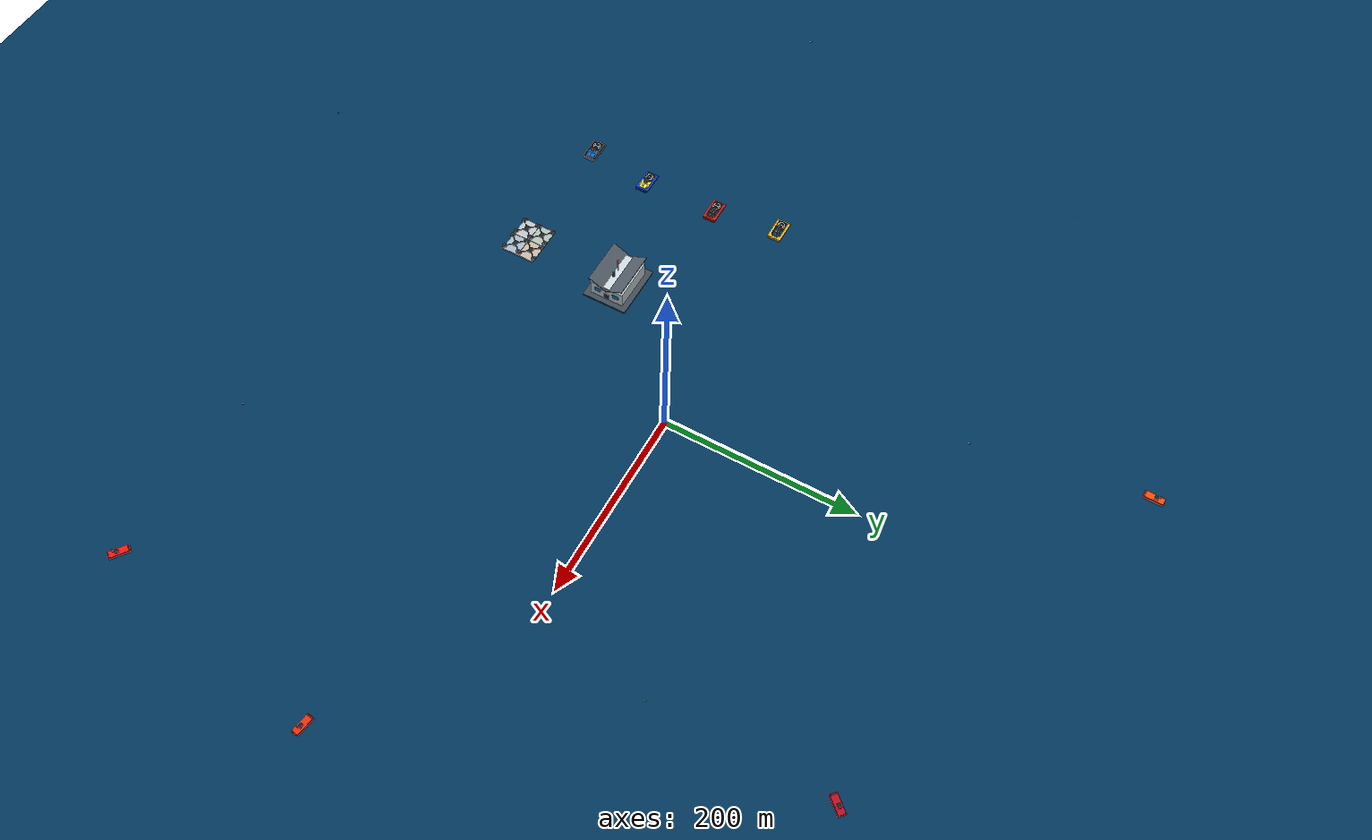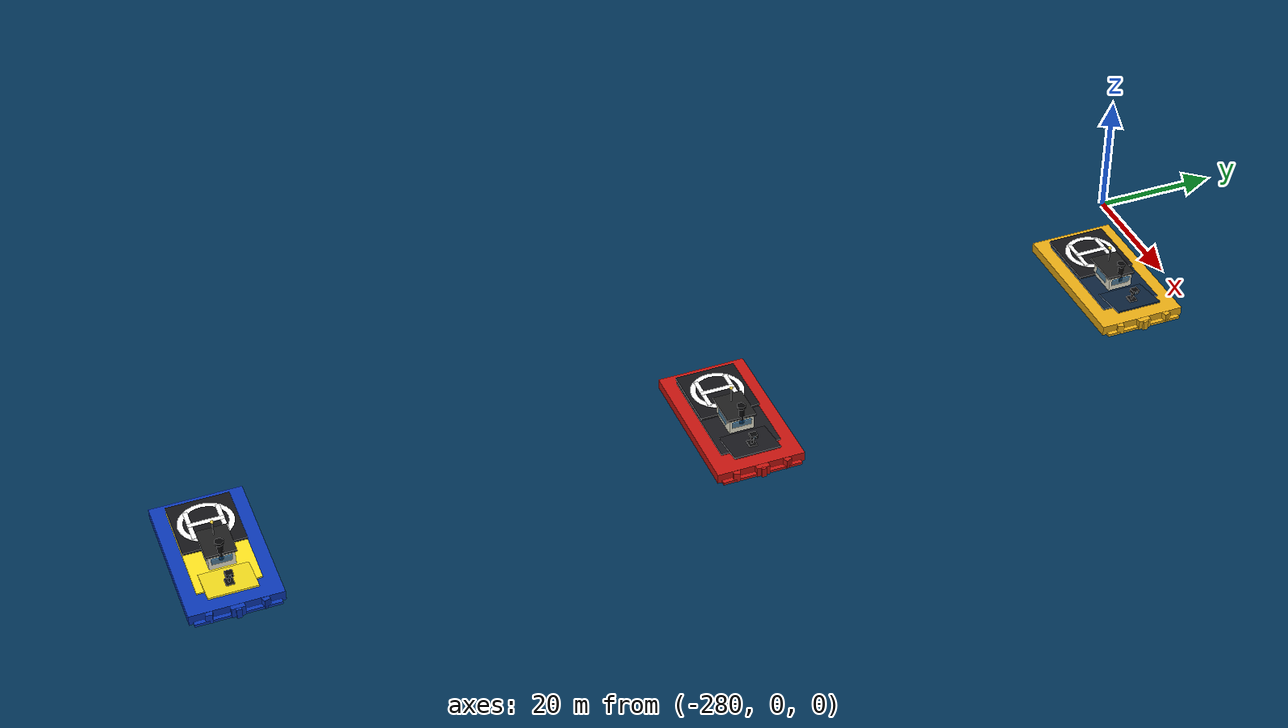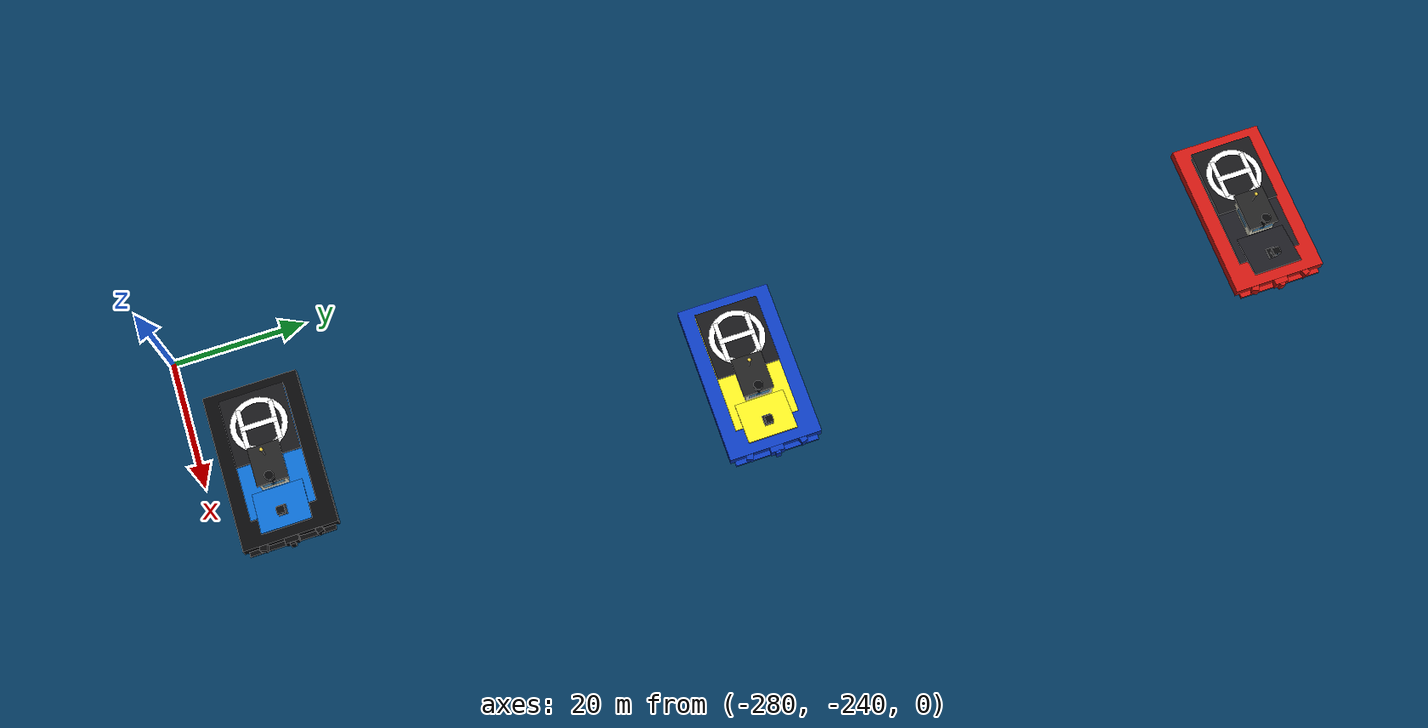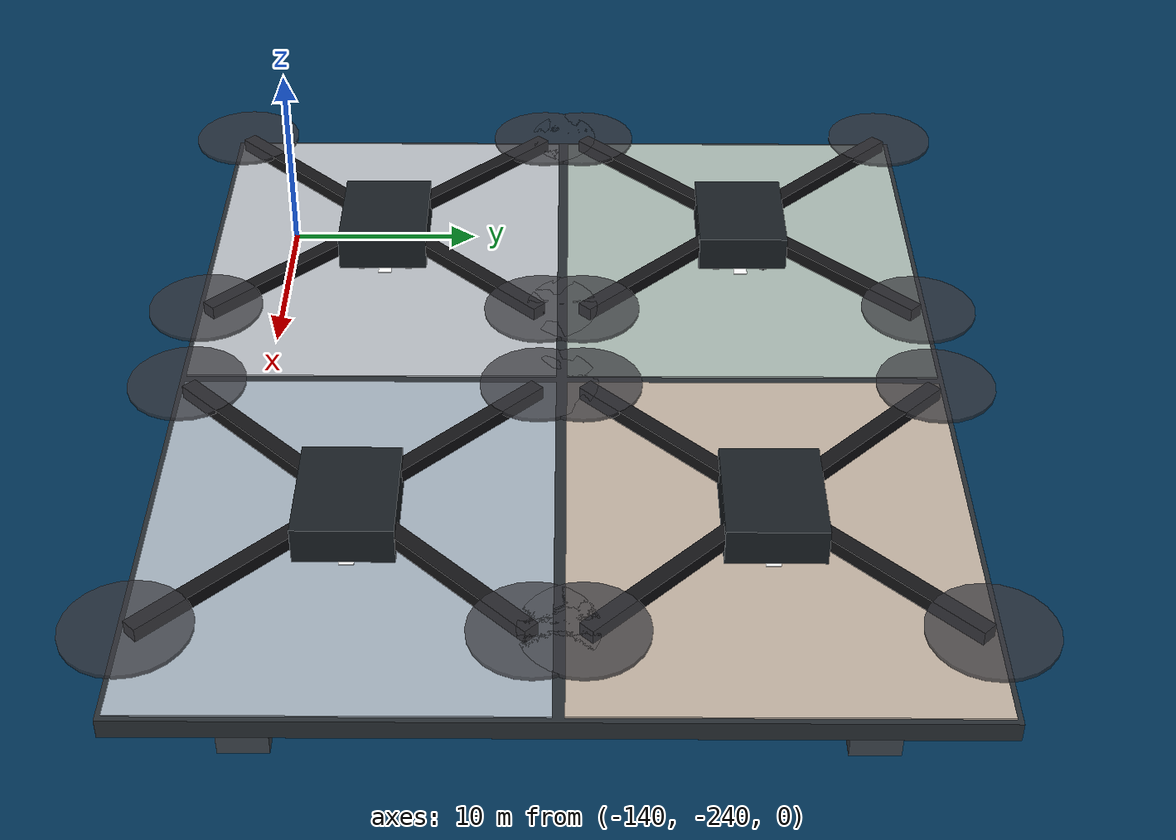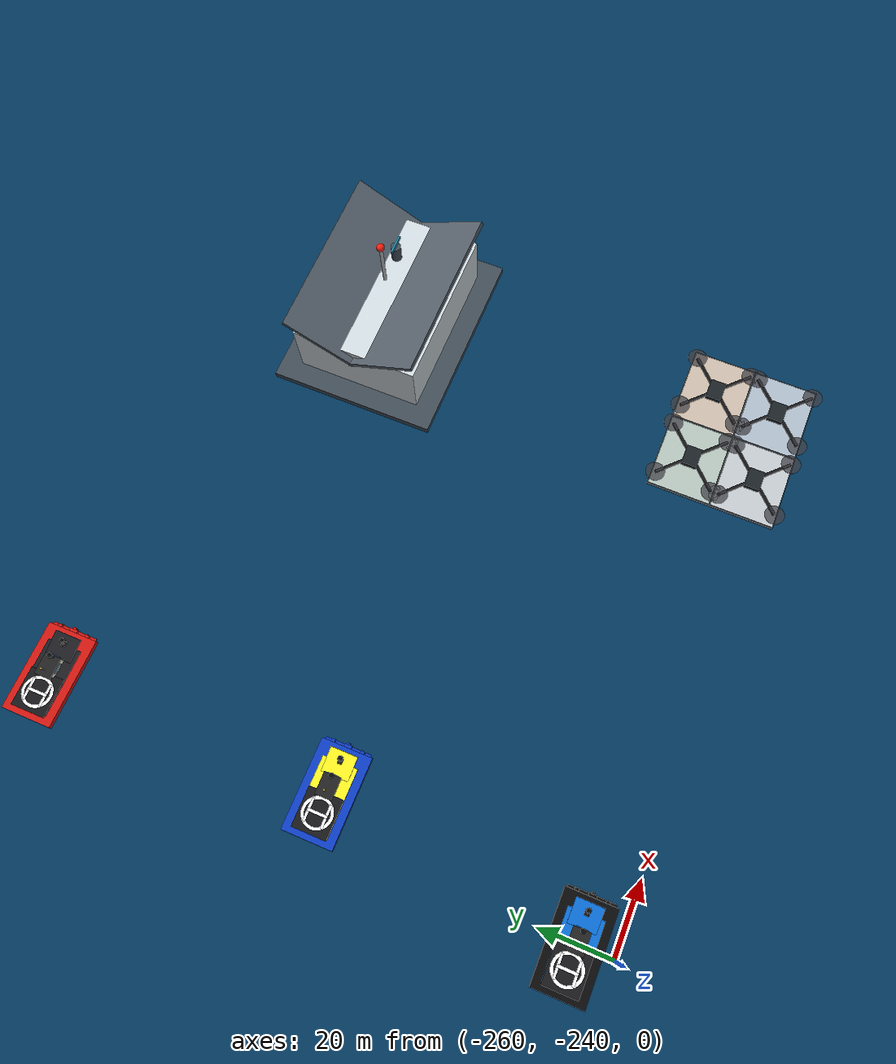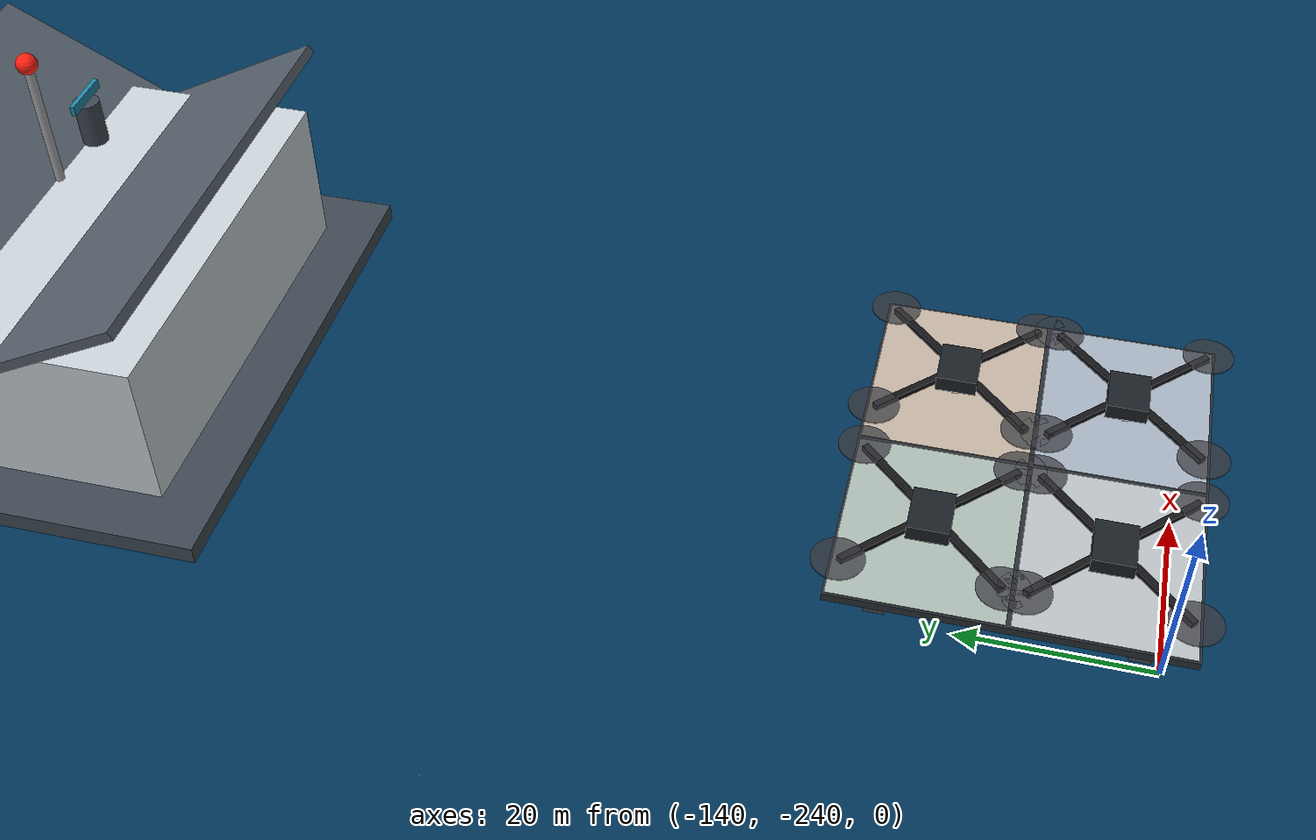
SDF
<sdf version="1.10">
 <world name="cooperative_response_sim">
  <plugin filename="gz-sim-physics-system" name="gz::sim::systems::Physics"/>
  <plugin filename="gz-sim-user-commands-system" name="gz::sim::systems::UserCommands"/>
  <plugin filename="gz-sim-scene-broadcaster-system" name="gz::sim::systems::SceneBroadcaster"/>
  <plugin filename="gz-sim-sensors-system" name="gz::sim::systems::Sensors">
   <render_engine>ogre2</render_engine>
  </plugin>
  <plugin filename="gz-sim-imu-system" name="gz::sim::systems::Imu"/>
  <plugin filename="gz-sim-air-pressure-system" name="gz::sim::systems::AirPressure"/>
  <plugin filename="gz-sim-navsat-system" name="gz::sim::systems::NavSat"/>
  <plugin filename="gz-sim-magnetometer-system" name="gz::sim::systems::Magnetometer"/>
  <physics type="ode">
   <max_step_size>0.004</max_step_size>
   <real_time_factor>1</real_time_factor>
   <real_time_update_rate>250</real_time_update_rate>
  </physics>
  <gravity>0 0 -9.8</gravity>
  <magnetic_field>6.0e-06 2.3e-05 -4.2e-05</magnetic_field>
  <spherical_coordinates>
   <surface_model>EARTH_WGS84</surface_model>
   <world_frame_orientation>ENU</world_frame_orientation>
   <latitude_deg>47.3979710577</latitude_deg>
   <longitude_deg>8.5461637398</longitude_deg>
   <elevation>0</elevation>
   <heading_deg>0</heading_deg>
  </spherical_coordinates>
  <scene>
   <grid>false</grid>
   <ambient>0.82 0.84 0.86 1</ambient>
   <background>1 1 1 1</background>
   <shadows>true</shadows>
  </scene>
  <model name="ocean_plane">
   <static>true</static>
   <link name="ocean_link">
    <visual name="ocean_visual">
     <pose>0 0 -0.02 0 0 0</pose>
     <geometry><plane><normal>0 0 1</normal><size>1400 1400</size></plane></geometry>
     <material>
      <ambient>0 0.08 0.16 0.55</ambient>
      <diffuse>0 0.2 0.34 0.55</diffuse>
      <specular>0.04 0.07 0.08 1</specular>
     </material>
    </visual>
    <collision name="ocean_collision">
     <geometry><plane><normal>0 0 1</normal><size>1400 1400</size></plane></geometry>
    </collision>
   </link>
  </model>
  <include>
   <name>command_base</name>
   <pose>-120 -120 0 0 0 0</pose>
   <uri>model://offshore_command_base</uri>
  </include>
  <include>
   <name>fleet_uav_platform</name>
   <pose>-120 -225 4 0 0 0</pose>
   <uri>model://quad_uav_platform</uri>
  </include>
  <include>
   <name>uav_01_large_visual</name>
   <pose>-131 -234 3.5 0 0 0</pose>
   <uri>model://large_uav_shell</uri>
  </include>
  <include>
   <name>uav_02_large_visual</name>
   <pose>-109 -234 3.5 0 0 0</pose>
   <uri>model://large_uav_shell</uri>
  </include>
  <include>
   <name>uav_03_large_visual</name>
   <pose>-131 -216 3.5 0 0 0</pose>
   <uri>model://large_uav_shell</uri>
  </include>
  <include>
   <name>uav_04_large_visual</name>
   <pose>-109 -216 3.5 0 0 0</pose>
   <uri>model://large_uav_shell</uri>
  </include>
  <plugin filename="libDroneDeckFollower.so" name="gz::sim::systems::DroneDeckFollower">
   <boat_name>x500_mono_cam_down_0</boat_name>
   <drone_name>uav_01_large_visual</drone_name>
   <deck_offset>0 0 -3.1 0 0 0</deck_offset>
   <release_after>1000000000</release_after>
   <release_topic>/visual/uav_01/release</release_topic>
  </plugin>
  <plugin filename="libDroneDeckFollower.so" name="gz::sim::systems::DroneDeckFollower">
   <boat_name>x500_mono_cam_down_1</boat_name>
   <drone_name>uav_02_large_visual</drone_name>
   <deck_offset>0 0 -3.1 0 0 0</deck_offset>
   <release_after>1000000000</release_after>
   <release_topic>/visual/uav_02/release</release_topic>
  </plugin>
  <plugin filename="libDroneDeckFollower.so" name="gz::sim::systems::DroneDeckFollower">
   <boat_name>x500_mono_cam_down_2</boat_name>
   <drone_name>uav_03_large_visual</drone_name>
   <deck_offset>0 0 -3.1 0 0 0</deck_offset>
   <release_after>1000000000</release_after>
   <release_topic>/visual/uav_03/release</release_topic>
  </plugin>
  <plugin filename="libDroneDeckFollower.so" name="gz::sim::systems::DroneDeckFollower">
   <boat_name>x500_mono_cam_down_3</boat_name>
   <drone_name>uav_04_large_visual</drone_name>
   <deck_offset>0 0 -3.1 0 0 0</deck_offset>
   <release_after>1000000000</release_after>
   <release_topic>/visual/uav_04/release</release_topic>
  </plugin>
  <include>
   <name>own_01</name>
   <pose>-260 -230 0.2 0 0 0</pose>
   <uri>model://cooperative_own_01_boat</uri>
  </include>
  <include>
   <name>own_02</name>
   <pose>-250 -160 0.2 0 0 0</pose>
   <uri>model://cooperative_own_02_boat</uri>
  </include>
  <include>
   <name>own_03</name>
   <pose>-250 -80 0.2 0 0 0</pose>
   <uri>model://cooperative_own_03_boat</uri>
  </include>
  <include>
   <name>own_04</name>
   <pose>-260 -10 0.2 0 0 0</pose>
   <uri>model://cooperative_own_04_boat</uri>
  </include>
  <include>
   <name>enemy_01</name>
   <pose>360 -360 0.2 0 0 2.5</pose>
   <uri>model://cooperative_enemy_01_boat</uri>
  </include>
  <include>
   <name>enemy_02</name>
   <pose>410 -120 0.2 0 0 3.0</pose>
   <uri>model://cooperative_enemy_02_boat</uri>
  </include>
  <include>
   <name>enemy_03</name>
   <pose>250 300 0.2 0 0 -2.3</pose>
   <uri>model://cooperative_enemy_03_boat</uri>
  </include>
  <include>
   <name>enemy_04</name>
   <pose>-150 430 0.2 0 0 -1.6</pose>
   <uri>model://cooperative_enemy_04_boat</uri>
  </include>
  <include><name>nav_buoy_north</name><pose>-120 260 0 0 0 0</pose><uri>model://medium_buoy</uri></include>
  <include>
   <name>nav_buoy_northeast</name>
   <pose>250 120 0 0 0 0</pose>
   <uri>model://green_channel_buoy</uri>
  </include>
  <include><name>nav_buoy_southeast</name><pose>180 -360 0 0 0 0</pose><uri>model://medium_buoy</uri></include>
  <include>
   <name>nav_buoy_south</name>
   <pose>-170 -500 0 0 0 0</pose>
   <uri>model://green_channel_buoy</uri>
  </include>
  <include><name>nav_buoy_west</name><pose>-520 -100 0 0 0 0</pose><uri>model://medium_buoy</uri></include>
  <include>
   <name>nav_buoy_northwest</name>
   <pose>-430 250 0 0 0 0</pose>
   <uri>model://green_channel_buoy</uri>
  </include>
  <light name="sun" type="directional">
   <pose>0 0 300 0 0 0</pose>
   <intensity>1.1</intensity>
   <direction>-0.35 0.15 -0.92</direction>
   <diffuse>0.9 0.9 0.86 1</diffuse>
   <specular>0.25 0.25 0.22 1</specular>
  </light>
 </world>
</sdf>

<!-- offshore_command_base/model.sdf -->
<sdf version="1.10">
  <model name="offshore_command_base">
    <static>true</static>
    <link name="building">
      <collision name="foundation_collision"><pose>0 0 1.0 0 0 0</pose><geometry><box><size>58 48 2</size></box></geometry></collision>
      <collision name="house_collision"><pose>0 0 10 0 0 0</pose><geometry><box><size>46 36 18</size></box></geometry></collision>
      <visual name="foundation"><pose>0 0 1.0 0 0 0</pose><geometry><box><size>58 48 2</size></box></geometry><material><ambient>0.12 0.14 0.16 1</ambient><diffuse>0.24 0.28 0.32 1</diffuse></material></visual>
      <visual name="house"><pose>0 0 10 0 0 0</pose><geometry><box><size>46 36 18</size></box></geometry><material><ambient>0.56 0.60 0.62 1</ambient><diffuse>0.78 0.82 0.84 1</diffuse><specular>0.2 0.2 0.2 1</specular></material></visual>
      <visual name="roof_left"><pose>0 9.1 21.2 0.48 0 0</pose><geometry><box><size>50 22 1.1</size></box></geometry><material><ambient>0.18 0.20 0.23 1</ambient><diffuse>0.32 0.36 0.40 1</diffuse></material></visual>
      <visual name="roof_right"><pose>0 -9.1 21.2 -0.48 0 0</pose><geometry><box><size>50 22 1.1</size></box></geometry><material><ambient>0.18 0.20 0.23 1</ambient><diffuse>0.32 0.36 0.40 1</diffuse></material></visual>
      <visual name="door"><pose>23.05 0 5.5 0 0 0</pose><geometry><box><size>0.25 6 9</size></box></geometry><material><ambient>0.08 0.10 0.12 1</ambient><diffuse>0.12 0.16 0.20 1</diffuse></material></visual>
      <visual name="window_1"><pose>23.1 10 11 0 0 0</pose><geometry><box><size>0.3 7 5</size></box></geometry><material><ambient>0.05 0.30 0.48 1</ambient><diffuse>0.10 0.48 0.72 1</diffuse><emissive>0.02 0.12 0.20 1</emissive></material></visual>
      <visual name="window_2"><pose>23.1 -10 11 0 0 0</pose><geometry><box><size>0.3 7 5</size></box></geometry><material><ambient>0.05 0.30 0.48 1</ambient><diffuse>0.10 0.48 0.72 1</diffuse><emissive>0.02 0.12 0.20 1</emissive></material></visual>
      <visual name="antenna"><pose>0 0 30 0 0 0</pose><geometry><cylinder><radius>0.5</radius><length>14</length></cylinder></geometry><material><ambient>0.35 0.36 0.38 1</ambient><diffuse>0.65 0.66 0.68 1</diffuse></material></visual>
      <visual name="beacon"><pose>0 0 37.3 0 0 0</pose><geometry><sphere><radius>1.1</radius></sphere></geometry><material><ambient>0.9 0.08 0.04 1</ambient><diffuse>1 0.12 0.06 1</diffuse><emissive>0.8 0.03 0.01 1</emissive></material></visual>
      <visual name="radar_pedestal"><pose>8 0 25 0 0 0</pose><geometry><cylinder><radius>1.4</radius><length>5</length></cylinder></geometry><material><ambient>0.12 0.14 0.16 1</ambient><diffuse>0.24 0.28 0.32 1</diffuse></material></visual>
      <visual name="radar_head"><pose>8 0 28 0 0 0</pose><geometry><box><size>5.5 0.5 1.1</size></box></geometry><material><ambient>0.08 0.22 0.28 1</ambient><diffuse>0.12 0.52 0.64 1</diffuse><emissive>0.02 0.12 0.16 1</emissive></material></visual>
      <sensor name="base_radar" type="gpu_lidar">
        <pose>8 0 28 0 0 0</pose>
        <topic>/base/radar/scan</topic>
        <update_rate>10</update_rate>
        <ray>
          <scan><horizontal><samples>720</samples><resolution>1</resolution><min_angle>-3.1415926</min_angle><max_angle>3.1415926</max_angle></horizontal></scan>
          <range><min>3</min><max>700</max><resolution>0.2</resolution></range>
          <noise><type>gaussian</type><mean>0</mean><stddev>0.03</stddev></noise>
        </ray>
        <always_on>true</always_on>
        <visualize>true</visualize>
      </sensor>
      <light name="base_beacon" type="point"><pose>0 0 37.3 0 0 0</pose><cast_shadows>false</cast_shadows><intensity>2</intensity><diffuse>1 0.16 0.08 1</diffuse><attenuation><range>100</range><constant>0.5</constant><linear>0.02</linear><quadratic>0.001</quadratic></attenuation></light>
    </link>
  </model>
</sdf>

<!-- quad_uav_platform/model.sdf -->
<sdf version="1.10">
  <model name="quad_uav_platform">
    <static>true</static>
    <link name="platform">
      <collision name="support_collision_1"><pose>-18 -13 -2 0 0 0</pose><geometry><box><size>2.2 2.2 4</size></box></geometry></collision>
      <collision name="support_collision_2"><pose>18 -13 -2 0 0 0</pose><geometry><box><size>2.2 2.2 4</size></box></geometry></collision>
      <collision name="support_collision_3"><pose>-18 13 -2 0 0 0</pose><geometry><box><size>2.2 2.2 4</size></box></geometry></collision>
      <collision name="support_collision_4"><pose>18 13 -2 0 0 0</pose><geometry><box><size>2.2 2.2 4</size></box></geometry></collision>
      <visual name="support_1"><pose>-18 -13 -2 0 0 0</pose><geometry><box><size>2.2 2.2 4</size></box></geometry><material><ambient>0.12 0.13 0.14 1</ambient><diffuse>0.24 0.27 0.30 1</diffuse></material></visual>
      <visual name="support_2"><pose>18 -13 -2 0 0 0</pose><geometry><box><size>2.2 2.2 4</size></box></geometry><material><ambient>0.12 0.13 0.14 1</ambient><diffuse>0.24 0.27 0.30 1</diffuse></material></visual>
      <visual name="support_3"><pose>-18 13 -2 0 0 0</pose><geometry><box><size>2.2 2.2 4</size></box></geometry><material><ambient>0.12 0.13 0.14 1</ambient><diffuse>0.24 0.27 0.30 1</diffuse></material></visual>
      <visual name="support_4"><pose>18 13 -2 0 0 0</pose><geometry><box><size>2.2 2.2 4</size></box></geometry><material><ambient>0.12 0.13 0.14 1</ambient><diffuse>0.24 0.27 0.30 1</diffuse></material></visual>
      <collision name="platform_collision">
        <pose>0 0 0.45 0 0 0</pose>
        <geometry><box><size>44 36 0.9</size></box></geometry>
      </collision>
      <visual name="platform_base">
        <pose>0 0 0.45 0 0 0</pose>
        <geometry><box><size>44 36 0.9</size></box></geometry>
        <material><ambient>0.08 0.09 0.10 1</ambient><diffuse>0.16 0.18 0.20 1</diffuse><specular>0.3 0.3 0.3 1</specular></material>
      </visual>
      <visual name="pad_1"><pose>-11 -9 0.94 0 0 0</pose><geometry><box><size>21.5 17.5 0.08</size></box></geometry><material><ambient>0.48 0.50 0.52 1</ambient><diffuse>0.72 0.74 0.76 1</diffuse></material></visual>
      <visual name="pad_2"><pose>11 -9 0.94 0 0 0</pose><geometry><box><size>21.5 17.5 0.08</size></box></geometry><material><ambient>0.42 0.46 0.50 1</ambient><diffuse>0.64 0.69 0.74 1</diffuse></material></visual>
      <visual name="pad_3"><pose>-11 9 0.94 0 0 0</pose><geometry><box><size>21.5 17.5 0.08</size></box></geometry><material><ambient>0.44 0.48 0.46 1</ambient><diffuse>0.66 0.72 0.69 1</diffuse></material></visual>
      <visual name="pad_4"><pose>11 9 0.94 0 0 0</pose><geometry><box><size>21.5 17.5 0.08</size></box></geometry><material><ambient>0.50 0.46 0.42 1</ambient><diffuse>0.75 0.69 0.63 1</diffuse></material></visual>
      <visual name="h1a"><pose>-11 -9 1.00 0 0 0</pose><geometry><box><size>4.2 0.65 0.06</size></box></geometry><material><ambient>1 1 1 1</ambient><diffuse>1 1 1 1</diffuse></material></visual>
      <visual name="h1b"><pose>-11 -9 1.01 0 0 1.5708</pose><geometry><box><size>3.2 0.65 0.06</size></box></geometry><material><ambient>1 1 1 1</ambient><diffuse>1 1 1 1</diffuse></material></visual>
      <visual name="h2a"><pose>11 -9 1.00 0 0 0</pose><geometry><box><size>4.2 0.65 0.06</size></box></geometry><material><ambient>1 1 1 1</ambient><diffuse>1 1 1 1</diffuse></material></visual>
      <visual name="h2b"><pose>11 -9 1.01 0 0 1.5708</pose><geometry><box><size>3.2 0.65 0.06</size></box></geometry><material><ambient>1 1 1 1</ambient><diffuse>1 1 1 1</diffuse></material></visual>
      <visual name="h3a"><pose>-11 9 1.00 0 0 0</pose><geometry><box><size>4.2 0.65 0.06</size></box></geometry><material><ambient>1 1 1 1</ambient><diffuse>1 1 1 1</diffuse></material></visual>
      <visual name="h3b"><pose>-11 9 1.01 0 0 1.5708</pose><geometry><box><size>3.2 0.65 0.06</size></box></geometry><material><ambient>1 1 1 1</ambient><diffuse>1 1 1 1</diffuse></material></visual>
      <visual name="h4a"><pose>11 9 1.00 0 0 0</pose><geometry><box><size>4.2 0.65 0.06</size></box></geometry><material><ambient>1 1 1 1</ambient><diffuse>1 1 1 1</diffuse></material></visual>
      <visual name="h4b"><pose>11 9 1.01 0 0 1.5708</pose><geometry><box><size>3.2 0.65 0.06</size></box></geometry><material><ambient>1 1 1 1</ambient><diffuse>1 1 1 1</diffuse></material></visual>
    </link>
  </model>
</sdf>

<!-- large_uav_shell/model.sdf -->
<sdf version="1.10">
  <model name="large_uav_shell">
    <static>true</static>
    <link name="visual_body">
      <visual name="body"><pose>0 0 3.1 0 0 0</pose><geometry><box><size>5.5 4.35 1.72</size></box></geometry><material><ambient>0.04 0.05 0.06 1</ambient><diffuse>0.10 0.12 0.14 1</diffuse><specular>0.5 0.5 0.5 1</specular></material></visual>
      <visual name="arm_1"><pose>4.1 4.1 3.2 0 0 0.7854</pose><geometry><box><size>10.8 0.74 0.63</size></box></geometry><material><ambient>0.03 0.03 0.035 1</ambient><diffuse>0.08 0.08 0.09 1</diffuse></material></visual>
      <visual name="arm_2"><pose>4.1 -4.1 3.2 0 0 -0.7854</pose><geometry><box><size>10.8 0.74 0.63</size></box></geometry><material><ambient>0.03 0.03 0.035 1</ambient><diffuse>0.08 0.08 0.09 1</diffuse></material></visual>
      <visual name="arm_3"><pose>-4.1 4.1 3.2 0 0 -0.7854</pose><geometry><box><size>10.8 0.74 0.63</size></box></geometry><material><ambient>0.03 0.03 0.035 1</ambient><diffuse>0.08 0.08 0.09 1</diffuse></material></visual>
      <visual name="arm_4"><pose>-4.1 -4.1 3.2 0 0 0.7854</pose><geometry><box><size>10.8 0.74 0.63</size></box></geometry><material><ambient>0.03 0.03 0.035 1</ambient><diffuse>0.08 0.08 0.09 1</diffuse></material></visual>
      <visual name="rotor_1"><pose>8 8 3.45 0 0 0</pose><geometry><cylinder><radius>2.7</radius><length>0.18</length></cylinder></geometry><material><ambient>0.12 0.12 0.13 0.75</ambient><diffuse>0.22 0.22 0.24 0.75</diffuse></material></visual>
      <visual name="rotor_2"><pose>8 -8 3.45 0 0 0</pose><geometry><cylinder><radius>2.7</radius><length>0.18</length></cylinder></geometry><material><ambient>0.12 0.12 0.13 0.75</ambient><diffuse>0.22 0.22 0.24 0.75</diffuse></material></visual>
      <visual name="rotor_3"><pose>-8 8 3.45 0 0 0</pose><geometry><cylinder><radius>2.7</radius><length>0.18</length></cylinder></geometry><material><ambient>0.12 0.12 0.13 0.75</ambient><diffuse>0.22 0.22 0.24 0.75</diffuse></material></visual>
      <visual name="rotor_4"><pose>-8 -8 3.45 0 0 0</pose><geometry><cylinder><radius>2.7</radius><length>0.18</length></cylinder></geometry><material><ambient>0.12 0.12 0.13 0.75</ambient><diffuse>0.22 0.22 0.24 0.75</diffuse></material></visual>
      <visual name="leg_1"><pose>1.5 1.2 1.4 0.15 0 0</pose><geometry><cylinder><radius>0.22</radius><length>2.8</length></cylinder></geometry><material><ambient>0.04 0.04 0.045 1</ambient><diffuse>0.10 0.10 0.11 1</diffuse></material></visual>
      <visual name="leg_2"><pose>1.5 -1.2 1.4 -0.15 0 0</pose><geometry><cylinder><radius>0.22</radius><length>2.8</length></cylinder></geometry><material><ambient>0.04 0.04 0.045 1</ambient><diffuse>0.10 0.10 0.11 1</diffuse></material></visual>
      <visual name="leg_3"><pose>-1.5 1.2 1.4 0.15 0 0</pose><geometry><cylinder><radius>0.22</radius><length>2.8</length></cylinder></geometry><material><ambient>0.04 0.04 0.045 1</ambient><diffuse>0.10 0.10 0.11 1</diffuse></material></visual>
      <visual name="leg_4"><pose>-1.5 -1.2 1.4 -0.15 0 0</pose><geometry><cylinder><radius>0.22</radius><length>2.8</length></cylinder></geometry><material><ambient>0.04 0.04 0.045 1</ambient><diffuse>0.10 0.10 0.11 1</diffuse></material></visual>
      <visual name="sensor"><pose>0 0 1.5 0 0 0</pose><geometry><box><size>1.5 1.5 1.2</size></box></geometry><material><ambient>0.55 0.45 0.02 1</ambient><diffuse>0.95 0.78 0.05 1</diffuse></material></visual>
    </link>
  </model>
</sdf>

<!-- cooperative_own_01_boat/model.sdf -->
<sdf version="1.8">
  <model name="cooperative_own_01_boat">
    <pose>0 0 1.70625 0 0 0</pose>
    <link name="hull">
      <enable_wind>true</enable_wind>
      <inertial>
        <mass>8897.85</mass>
        <inertia>
          <ixx>76690.56915</ixx>
          <iyy>162403.5582</iyy>
          <izz>198493.2378</izz>
          <ixy>0</ixy>
          <ixz>0</ixz>
          <iyz>0</iyz>
        </inertia>
      </inertial>
      <collision name="hull_collision">
        <pose>0 0 -0.24375 0 0 0</pose>
        <geometry>
          <box>
            <size>21.879 12.2265 2.4375</size>
          </box>
        </geometry>
      </collision>
      <visual name="lower_hull">
        <pose>-0.32175 0 -0.78 0 0 0</pose>
        <geometry>
          <box>
            <size>25.0965 12.7413 1.638</size>
          </box>
        </geometry>
        <material>
          <ambient>0.015 0.015 0.018 1</ambient>
          <diffuse>0.025 0.025 0.030 1</diffuse>
          <specular>0.1 0.1 0.1 1</specular>
        </material>
      </visual>
      <visual name="upper_hull">
        <pose>-0.6435 0 0.24375 0 0 0</pose>
        <geometry>
          <box>
            <size>24.3243 14.05404 1.872</size>
          </box>
        </geometry>
        <material>
          <ambient>0.015 0.015 0.018 1</ambient>
          <diffuse>0.025 0.025 0.030 1</diffuse>
          <specular>0.18 0.18 0.2 1</specular>
        </material>
      </visual>
      <visual name="bow_side_left">
        <pose>9.3951 3.3462 0.195 0 0 0.31</pose>
        <geometry>
          <box>
            <size>5.9202 1.0296 1.8525</size>
          </box>
        </geometry>
        <material>
          <ambient>0.015 0.015 0.018 1</ambient>
          <diffuse>0.025 0.025 0.030 1</diffuse>
          <specular>0.18 0.18 0.2 1</specular>
        </material>
      </visual>
      <visual name="bow_side_right">
        <pose>9.3951 -3.3462 0.195 0 0 -0.31</pose>
        <geometry>
          <box>
            <size>5.9202 1.0296 1.8525</size>
          </box>
        </geometry>
        <material>
          <ambient>0.015 0.015 0.018 1</ambient>
          <diffuse>0.025 0.025 0.030 1</diffuse>
          <specular>0.18 0.18 0.2 1</specular>
        </material>
      </visual>
      <visual name="bow_center_nose">
        <pose>11.7117 0 0.195 0 0 0</pose>
        <geometry>
          <box>
            <size>1.287 2.0592 1.95</size>
          </box>
        </geometry>
        <material>
          <ambient>0.015 0.015 0.018 1</ambient>
          <diffuse>0.025 0.025 0.030 1</diffuse>
          <specular>0.16 0.16 0.18 1</specular>
        </material>
      </visual>
      <visual name="bow_keel_line">
        <pose>9.97425 0 -1.6575 0 1.5708 0</pose>
        <geometry>
          <cylinder>
            <radius>0.1365</radius>
            <length>3.51</length>
          </cylinder>
        </geometry>
        <material>
          <ambient>0.006 0.006 0.008 1</ambient>
          <diffuse>0.012 0.012 0.014 1</diffuse>
        </material>
      </visual>
      <visual name="foredeck_slope">
        <pose>6.75675 0 1.755 0 -0.16 0</pose>
        <geometry>
          <box>
            <size>7.0785 7.4646 0.268125</size>
          </box>
        </geometry>
        <material>
          <ambient>0.02 0.18 0.35 1</ambient>
          <diffuse>0.03 0.40 0.78 1</diffuse>
          <specular>0.08 0.08 0.08 1</specular>
        </material>
      </visual>
      <visual name="bow_stem">
        <pose>12.4839 0 0.14625 0 0 0</pose>
        <geometry>
          <box>
            <size>0.5148 0.7722 2.0475</size>
          </box>
        </geometry>
        <material>
          <ambient>0.015 0.015 0.018 1</ambient>
          <diffuse>0.025 0.025 0.030 1</diffuse>
          <specular>0.16 0.16 0.18 1</specular>
        </material>
      </visual>
      <visual name="hull_side_fairing_left">
        <pose>0.32175 5.5341 0.195 0 0 0.035</pose>
        <geometry>
          <box>
            <size>17.05275 0.5148 1.0725</size>
          </box>
        </geometry>
        <material>
          <ambient>0.015 0.015 0.018 1</ambient>
          <diffuse>0.025 0.025 0.030 1</diffuse>
          <specular>0.14 0.14 0.16 1</specular>
        </material>
      </visual>
      <visual name="hull_side_fairing_right">
        <pose>0.32175 -5.5341 0.195 0 0 -0.035</pose>
        <geometry>
          <box>
            <size>17.05275 0.5148 1.0725</size>
          </box>
        </geometry>
        <material>
          <ambient>0.015 0.015 0.018 1</ambient>
          <diffuse>0.025 0.025 0.030 1</diffuse>
          <specular>0.14 0.14 0.16 1</specular>
        </material>
      </visual>
      <visual name="deck">
        <pose>-1.60875 0 1.21875 0 0 0</pose>
        <geometry>
          <box>
            <size>18.33975 9.6525 0.39</size>
          </box>
        </geometry>
        <material>
          <ambient>0.02 0.18 0.35 1</ambient>
          <diffuse>0.03 0.40 0.78 1</diffuse>
          <specular>0.08 0.08 0.08 1</specular>
        </material>
      </visual>
      <visual name="cabin_body">
        <pose>1.287 0 2.8275 0 0 0</pose>
        <geometry>
          <box>
            <size>5.0193 3.9897 2.34</size>
          </box>
        </geometry>
        <material>
          <ambient>0.86 0.86 0.8 1</ambient>
          <diffuse>0.96 0.95 0.86 1</diffuse>
          <specular>0.28 0.28 0.24 1</specular>
        </material>
      </visual>
      <visual name="front_window">
        <pose>3.861 0 3.12 0 0.28 0</pose>
        <geometry>
          <box>
            <size>0.225225 3.0888 1.17</size>
          </box>
        </geometry>
        <material>
          <ambient>0.05 0.22 0.36 0.65</ambient>
          <diffuse>0.08 0.38 0.62 0.65</diffuse>
          <specular>0.9 0.95 1 1</specular>
        </material>
      </visual>
      <visual name="left_window">
        <pose>1.287 2.091375 3.12 0 0 0</pose>
        <geometry>
          <box>
            <size>2.89575 0.160875 1.0725</size>
          </box>
        </geometry>
        <material>
          <ambient>0.05 0.22 0.36 0.65</ambient>
          <diffuse>0.08 0.38 0.62 0.65</diffuse>
          <specular>0.9 0.95 1 1</specular>
        </material>
      </visual>
      <visual name="right_window">
        <pose>1.287 -2.091375 3.12 0 0 0</pose>
        <geometry>
          <box>
            <size>2.89575 0.160875 1.0725</size>
          </box>
        </geometry>
        <material>
          <ambient>0.05 0.22 0.36 0.65</ambient>
          <diffuse>0.08 0.38 0.62 0.65</diffuse>
          <specular>0.9 0.95 1 1</specular>
        </material>
      </visual>
      <visual name="cabin_roof">
        <pose>0.96525 0 4.14375 0 0 0</pose>
        <geometry>
          <box>
            <size>5.9202 4.6332 0.39</size>
          </box>
        </geometry>
        <material>
          <ambient>0.08 0.08 0.08 1</ambient>
          <diffuse>0.12 0.12 0.12 1</diffuse>
          <specular>0.18 0.18 0.18 1</specular>
        </material>
      </visual>
      <collision name="landing_pad_collision">
        <pose>-5.9202 0 1.755 0 0 0</pose>
        <geometry>
          <box>
            <size>10.9395 9.97425 1.17</size>
          </box>
        </geometry>
        <surface>
          <contact>
            <ode>
              <min_depth>0.001</min_depth>
              <max_vel>0</max_vel>
            </ode>
          </contact>
          <friction>
            <ode>
              <mu>1.5</mu>
              <mu2>1.5</mu2>
            </ode>
          </friction>
        </surface>
      </collision>
      <visual name="landing_pad_visual">
        <pose>-5.9202 0 1.8525 0 0 0</pose>
        <geometry>
          <box>
            <size>10.608 9.594 0.39</size>
          </box>
        </geometry>
        <material>
          <ambient>0.04 0.04 0.045 1</ambient>
          <diffuse>0.08 0.08 0.09 1</diffuse>
          <specular>0.08 0.08 0.08 1</specular>
        </material>
      </visual>
      <visual name="landing_pad_ring">
        <pose>-5.9202 0 2.120625 0 0 0</pose>
        <geometry>
          <cylinder>
            <radius>4.212</radius>
            <length>0.0585</length>
          </cylinder>
        </geometry>
        <material>
          <ambient>1 1 1 1</ambient>
          <diffuse>1 1 1 1</diffuse>
        </material>
      </visual>
      <visual name="landing_pad_center">
        <pose>-5.9202 0 2.169375 0 0 0</pose>
        <geometry>
          <cylinder>
            <radius>3.354</radius>
            <length>0.06825</length>
          </cylinder>
        </geometry>
        <material>
          <ambient>0.04 0.04 0.045 1</ambient>
          <diffuse>0.08 0.08 0.09 1</diffuse>
        </material>
      </visual>
      <visual name="landing_h_left">
        <pose>-5.9202 2.418 2.23275 0 0 0</pose>
        <geometry>
          <box>
            <size>6.045 0.702 0.0585</size>
          </box>
        </geometry>
        <material>
          <ambient>1 1 1 1</ambient>
          <diffuse>1 1 1 1</diffuse>
        </material>
      </visual>
      <visual name="landing_h_right">
        <pose>-5.9202 -2.418 2.23275 0 0 0</pose>
        <geometry>
          <box>
            <size>6.045 0.702 0.0585</size>
          </box>
        </geometry>
        <material>
          <ambient>1 1 1 1</ambient>
          <diffuse>1 1 1 1</diffuse>
        </material>
      </visual>
      <visual name="landing_h_crossbar">
        <pose>-5.9202 0 2.25225 0 0 0</pose>
        <geometry>
          <box>
            <size>0.78 5.538 0.0585</size>
          </box>
        </geometry>
        <material>
          <ambient>1 1 1 1</ambient>
          <diffuse>1 1 1 1</diffuse>
        </material>
      </visual>
      <visual name="mast">
        <pose>-0.32175 0 5.3625 0 0 0</pose>
        <geometry>
          <cylinder>
            <radius>0.08775</radius>
            <length>2.68125</length>
          </cylinder>
        </geometry>
        <material>
          <ambient>0.02 0.02 0.02 1</ambient>
          <diffuse>0.02 0.02 0.02 1</diffuse>
        </material>
      </visual>
      <visual name="nav_light">
        <pose>-0.32175 0 6.77625 0 0 0</pose>
        <geometry>
          <sphere>
            <radius>0.268125</radius>
          </sphere>
        </geometry>
        <material>
          <ambient>1 0.85 0.25 1</ambient>
          <diffuse>1 0.85 0.25 1</diffuse>
          <specular>1 0.9 0.5 1</specular>
        </material>
      </visual>
      <visual name="lidar_mount">
        <pose>3.53925 0 4.5825 0 0 0</pose>
        <geometry>
          <cylinder>
            <radius>0.43875</radius>
            <length>3.0225</length>
          </cylinder>
        </geometry>
        <material>
          <ambient>0.02 0.02 0.022 1</ambient>
          <diffuse>0.04 0.04 0.045 1</diffuse>
          <specular>0.2 0.2 0.22 1</specular>
        </material>
      </visual>
      <visual name="lidar_body">
        <pose>3.53925 0 6.19125 0 0 0</pose>
        <geometry>
          <cylinder>
            <radius>0.6825</radius>
            <length>0.39</length>
          </cylinder>
        </geometry>
        <material>
          <ambient>0.01 0.01 0.012 1</ambient>
          <diffuse>0.02 0.02 0.024 1</diffuse>
          <specular>0.35 0.35 0.38 1</specular>
        </material>
      </visual>
      <visual name="front_camera_mount_base">
        <pose>7.722 0 2.218125 0 0 0</pose>
        <geometry>
          <box>
            <size>1.5444 1.287 0.195</size>
          </box>
        </geometry>
        <material>
          <ambient>0.025 0.025 0.028 1</ambient>
          <diffuse>0.04 0.04 0.045 1</diffuse>
          <specular>0.18 0.18 0.2 1</specular>
        </material>
      </visual>
      <visual name="front_camera_mount_post">
        <pose>7.722 0 3.16875 0 0 0</pose>
        <geometry>
          <cylinder>
            <radius>0.170625</radius>
            <length>1.70625</length>
          </cylinder>
        </geometry>
        <material>
          <ambient>0.018 0.018 0.02 1</ambient>
          <diffuse>0.03 0.03 0.034 1</diffuse>
          <specular>0.18 0.18 0.2 1</specular>
        </material>
      </visual>
      <visual name="front_camera_body">
        <pose>8.30115 0 4.1925 0 0 0</pose>
        <geometry>
          <box>
            <size>1.0296 1.1583 0.585</size>
          </box>
        </geometry>
        <material>
          <ambient>0.015 0.015 0.018 1</ambient>
          <diffuse>0.025 0.025 0.03 1</diffuse>
          <specular>0.2 0.2 0.22 1</specular>
        </material>
      </visual>
      <visual name="front_camera_lens">
        <pose>8.912475 0 4.1925 0 1.5708 0</pose>
        <geometry>
          <cylinder>
            <radius>0.219375</radius>
            <length>0.121875</length>
          </cylinder>
        </geometry>
        <material>
          <ambient>0.02 0.04 0.06 1</ambient>
          <diffuse>0.03 0.08 0.12 1</diffuse>
          <specular>0.8 0.9 1 1</specular>
        </material>
      </visual>
      <sensor name="front_camera" type="camera">
        <pose>9.041175 0 4.1925 0 0 0</pose>
        <topic>/defense/own_01/front_camera</topic>
        <update_rate>30</update_rate>
        <camera>
          <horizontal_fov>1.047</horizontal_fov>
          <image>
            <width>320</width>
            <height>180</height>
            <format>R8G8B8</format>
          </image>
          <clip>
            <near>0.05</near>
            <far>200</far>
          </clip>
        </camera>
        <always_on>true</always_on>
        <visualize>false</visualize>
      </sensor>
      <sensor name="front_lidar" type="gpu_lidar">
        <gz_frame_id>own_01/hull/front_lidar</gz_frame_id>
        <pose>3.53925 0 6.09375 0 0 0</pose>
        <topic>/defense/own_01/scan</topic>
        <update_rate>10</update_rate>
        <ray>
          <scan>
            <horizontal>
              <samples>361</samples>
              <resolution>1</resolution>
              <min_angle>-1.5708</min_angle>
              <max_angle>1.5708</max_angle>
            </horizontal>
          </scan>
          <range>
            <min>0.35</min>
            <max>80</max>
            <resolution>0.02</resolution>
          </range>
          <noise>
            <type>gaussian</type>
            <mean>0</mean>
            <stddev>0.01</stddev>
          </noise>
          <visibility_mask>0x01</visibility_mask>
        </ray>
        <always_on>true</always_on>
        <visualize>false</visualize>
      </sensor>
    </link>
    <plugin filename="gz-sim-velocity-control-system" name="gz::sim::systems::VelocityControl">
      <topic>/model/own_01/cmd_vel</topic>
      <control_linear_velocity>true</control_linear_velocity>
      <control_angular_velocity>true</control_angular_velocity>
    </plugin>
    <plugin filename="gz-sim-pose-publisher-system" name="gz::sim::systems::PosePublisher">
      <publish_model_pose>true</publish_model_pose>
      <publish_link_pose>false</publish_link_pose>
      <publish_collision_pose>false</publish_collision_pose>
      <publish_visual_pose>false</publish_visual_pose>
      <publish_nested_model_pose>false</publish_nested_model_pose>
      <publish_sensor_pose>false</publish_sensor_pose>
      <use_pose_vector_msg>false</use_pose_vector_msg>
      /defense/own_01/pose
      <update_frequency>30</update_frequency>
    </plugin>
    <plugin filename="libBoatWaveFollower.so" name="gz::sim::systems::BoatWaveFollower">
      <mean_z>2.145</mean_z>
      <heave_amplitude>0.429</heave_amplitude>
      <roll_amplitude>0.055</roll_amplitude>
      <pitch_amplitude>0.045</pitch_amplitude>
      <primary_frequency>1.1</primary_frequency>
      <secondary_frequency>1.7</secondary_frequency>
      <wave_number_x>0.35</wave_number_x>
      <wave_number_y>0.22</wave_number_y>
    </plugin>
  </model>
</sdf>

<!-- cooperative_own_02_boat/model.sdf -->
<sdf version="1.8">
  <model name="cooperative_own_02_boat">
    <pose>0 0 1.70625 0 0 0</pose>
    <link name="hull">
      <enable_wind>true</enable_wind>
      <inertial>
        <mass>8897.85</mass>
        <inertia>
          <ixx>76690.56915</ixx>
          <iyy>162403.5582</iyy>
          <izz>198493.2378</izz>
          <ixy>0</ixy>
          <ixz>0</ixz>
          <iyz>0</iyz>
        </inertia>
      </inertial>
      <collision name="hull_collision">
        <pose>0 0 -0.24375 0 0 0</pose>
        <geometry>
          <box>
            <size>21.879 12.2265 2.4375</size>
          </box>
        </geometry>
      </collision>
      <visual name="lower_hull">
        <pose>-0.32175 0 -0.78 0 0 0</pose>
        <geometry>
          <box>
            <size>25.0965 12.7413 1.638</size>
          </box>
        </geometry>
        <material>
          <ambient>0.02 0.10 0.28 1</ambient>
          <diffuse>0.04 0.22 0.72 1</diffuse>
          <specular>0.1 0.1 0.1 1</specular>
        </material>
      </visual>
      <visual name="upper_hull">
        <pose>-0.6435 0 0.24375 0 0 0</pose>
        <geometry>
          <box>
            <size>24.3243 14.05404 1.872</size>
          </box>
        </geometry>
        <material>
          <ambient>0.02 0.10 0.28 1</ambient>
          <diffuse>0.04 0.22 0.72 1</diffuse>
          <specular>0.18 0.18 0.2 1</specular>
        </material>
      </visual>
      <visual name="bow_side_left">
        <pose>9.3951 3.3462 0.195 0 0 0.31</pose>
        <geometry>
          <box>
            <size>5.9202 1.0296 1.8525</size>
          </box>
        </geometry>
        <material>
          <ambient>0.02 0.10 0.28 1</ambient>
          <diffuse>0.04 0.22 0.72 1</diffuse>
          <specular>0.18 0.18 0.2 1</specular>
        </material>
      </visual>
      <visual name="bow_side_right">
        <pose>9.3951 -3.3462 0.195 0 0 -0.31</pose>
        <geometry>
          <box>
            <size>5.9202 1.0296 1.8525</size>
          </box>
        </geometry>
        <material>
          <ambient>0.02 0.10 0.28 1</ambient>
          <diffuse>0.04 0.22 0.72 1</diffuse>
          <specular>0.18 0.18 0.2 1</specular>
        </material>
      </visual>
      <visual name="bow_center_nose">
        <pose>11.7117 0 0.195 0 0 0</pose>
        <geometry>
          <box>
            <size>1.287 2.0592 1.95</size>
          </box>
        </geometry>
        <material>
          <ambient>0.02 0.10 0.28 1</ambient>
          <diffuse>0.04 0.22 0.72 1</diffuse>
          <specular>0.16 0.16 0.18 1</specular>
        </material>
      </visual>
      <visual name="bow_keel_line">
        <pose>9.97425 0 -1.6575 0 1.5708 0</pose>
        <geometry>
          <cylinder>
            <radius>0.1365</radius>
            <length>3.51</length>
          </cylinder>
        </geometry>
        <material>
          <ambient>0.006 0.006 0.008 1</ambient>
          <diffuse>0.012 0.012 0.014 1</diffuse>
        </material>
      </visual>
      <visual name="foredeck_slope">
        <pose>6.75675 0 1.755 0 -0.16 0</pose>
        <geometry>
          <box>
            <size>7.0785 7.4646 0.268125</size>
          </box>
        </geometry>
        <material>
          <ambient>0.75 0.75 0.08 1</ambient>
          <diffuse>1.00 0.90 0.12 1</diffuse>
          <specular>0.08 0.08 0.08 1</specular>
        </material>
      </visual>
      <visual name="bow_stem">
        <pose>12.4839 0 0.14625 0 0 0</pose>
        <geometry>
          <box>
            <size>0.5148 0.7722 2.0475</size>
          </box>
        </geometry>
        <material>
          <ambient>0.02 0.10 0.28 1</ambient>
          <diffuse>0.04 0.22 0.72 1</diffuse>
          <specular>0.16 0.16 0.18 1</specular>
        </material>
      </visual>
      <visual name="hull_side_fairing_left">
        <pose>0.32175 5.5341 0.195 0 0 0.035</pose>
        <geometry>
          <box>
            <size>17.05275 0.5148 1.0725</size>
          </box>
        </geometry>
        <material>
          <ambient>0.02 0.10 0.28 1</ambient>
          <diffuse>0.04 0.22 0.72 1</diffuse>
          <specular>0.14 0.14 0.16 1</specular>
        </material>
      </visual>
      <visual name="hull_side_fairing_right">
        <pose>0.32175 -5.5341 0.195 0 0 -0.035</pose>
        <geometry>
          <box>
            <size>17.05275 0.5148 1.0725</size>
          </box>
        </geometry>
        <material>
          <ambient>0.02 0.10 0.28 1</ambient>
          <diffuse>0.04 0.22 0.72 1</diffuse>
          <specular>0.14 0.14 0.16 1</specular>
        </material>
      </visual>
      <visual name="deck">
        <pose>-1.60875 0 1.21875 0 0 0</pose>
        <geometry>
          <box>
            <size>18.33975 9.6525 0.39</size>
          </box>
        </geometry>
        <material>
          <ambient>0.75 0.75 0.08 1</ambient>
          <diffuse>1.00 0.90 0.12 1</diffuse>
          <specular>0.08 0.08 0.08 1</specular>
        </material>
      </visual>
      <visual name="cabin_body">
        <pose>1.287 0 2.8275 0 0 0</pose>
        <geometry>
          <box>
            <size>5.0193 3.9897 2.34</size>
          </box>
        </geometry>
        <material>
          <ambient>0.86 0.86 0.8 1</ambient>
          <diffuse>0.96 0.95 0.86 1</diffuse>
          <specular>0.28 0.28 0.24 1</specular>
        </material>
      </visual>
      <visual name="front_window">
        <pose>3.861 0 3.12 0 0.28 0</pose>
        <geometry>
          <box>
            <size>0.225225 3.0888 1.17</size>
          </box>
        </geometry>
        <material>
          <ambient>0.05 0.22 0.36 0.65</ambient>
          <diffuse>0.08 0.38 0.62 0.65</diffuse>
          <specular>0.9 0.95 1 1</specular>
        </material>
      </visual>
      <visual name="left_window">
        <pose>1.287 2.091375 3.12 0 0 0</pose>
        <geometry>
          <box>
            <size>2.89575 0.160875 1.0725</size>
          </box>
        </geometry>
        <material>
          <ambient>0.05 0.22 0.36 0.65</ambient>
          <diffuse>0.08 0.38 0.62 0.65</diffuse>
          <specular>0.9 0.95 1 1</specular>
        </material>
      </visual>
      <visual name="right_window">
        <pose>1.287 -2.091375 3.12 0 0 0</pose>
        <geometry>
          <box>
            <size>2.89575 0.160875 1.0725</size>
          </box>
        </geometry>
        <material>
          <ambient>0.05 0.22 0.36 0.65</ambient>
          <diffuse>0.08 0.38 0.62 0.65</diffuse>
          <specular>0.9 0.95 1 1</specular>
        </material>
      </visual>
      <visual name="cabin_roof">
        <pose>0.96525 0 4.14375 0 0 0</pose>
        <geometry>
          <box>
            <size>5.9202 4.6332 0.39</size>
          </box>
        </geometry>
        <material>
          <ambient>0.08 0.08 0.08 1</ambient>
          <diffuse>0.12 0.12 0.12 1</diffuse>
          <specular>0.18 0.18 0.18 1</specular>
        </material>
      </visual>
      <collision name="landing_pad_collision">
        <pose>-5.9202 0 1.755 0 0 0</pose>
        <geometry>
          <box>
            <size>10.9395 9.97425 1.17</size>
          </box>
        </geometry>
        <surface>
          <contact>
            <ode>
              <min_depth>0.001</min_depth>
              <max_vel>0</max_vel>
            </ode>
          </contact>
          <friction>
            <ode>
              <mu>1.5</mu>
              <mu2>1.5</mu2>
            </ode>
          </friction>
        </surface>
      </collision>
      <visual name="landing_pad_visual">
        <pose>-5.9202 0 1.8525 0 0 0</pose>
        <geometry>
          <box>
            <size>10.608 9.594 0.39</size>
          </box>
        </geometry>
        <material>
          <ambient>0.04 0.04 0.045 1</ambient>
          <diffuse>0.08 0.08 0.09 1</diffuse>
          <specular>0.08 0.08 0.08 1</specular>
        </material>
      </visual>
      <visual name="landing_pad_ring">
        <pose>-5.9202 0 2.120625 0 0 0</pose>
        <geometry>
          <cylinder>
            <radius>4.212</radius>
            <length>0.0585</length>
          </cylinder>
        </geometry>
        <material>
          <ambient>1 1 1 1</ambient>
          <diffuse>1 1 1 1</diffuse>
        </material>
      </visual>
      <visual name="landing_pad_center">
        <pose>-5.9202 0 2.169375 0 0 0</pose>
        <geometry>
          <cylinder>
            <radius>3.354</radius>
            <length>0.06825</length>
          </cylinder>
        </geometry>
        <material>
          <ambient>0.04 0.04 0.045 1</ambient>
          <diffuse>0.08 0.08 0.09 1</diffuse>
        </material>
      </visual>
      <visual name="landing_h_left">
        <pose>-5.9202 2.418 2.23275 0 0 0</pose>
        <geometry>
          <box>
            <size>6.045 0.702 0.0585</size>
          </box>
        </geometry>
        <material>
          <ambient>1 1 1 1</ambient>
          <diffuse>1 1 1 1</diffuse>
        </material>
      </visual>
      <visual name="landing_h_right">
        <pose>-5.9202 -2.418 2.23275 0 0 0</pose>
        <geometry>
          <box>
            <size>6.045 0.702 0.0585</size>
          </box>
        </geometry>
        <material>
          <ambient>1 1 1 1</ambient>
          <diffuse>1 1 1 1</diffuse>
        </material>
      </visual>
      <visual name="landing_h_crossbar">
        <pose>-5.9202 0 2.25225 0 0 0</pose>
        <geometry>
          <box>
            <size>0.78 5.538 0.0585</size>
          </box>
        </geometry>
        <material>
          <ambient>1 1 1 1</ambient>
          <diffuse>1 1 1 1</diffuse>
        </material>
      </visual>
      <visual name="mast">
        <pose>-0.32175 0 5.3625 0 0 0</pose>
        <geometry>
          <cylinder>
            <radius>0.08775</radius>
            <length>2.68125</length>
          </cylinder>
        </geometry>
        <material>
          <ambient>0.02 0.02 0.02 1</ambient>
          <diffuse>0.02 0.02 0.02 1</diffuse>
        </material>
      </visual>
      <visual name="nav_light">
        <pose>-0.32175 0 6.77625 0 0 0</pose>
        <geometry>
          <sphere>
            <radius>0.268125</radius>
          </sphere>
        </geometry>
        <material>
          <ambient>1 0.85 0.25 1</ambient>
          <diffuse>1 0.85 0.25 1</diffuse>
          <specular>1 0.9 0.5 1</specular>
        </material>
      </visual>
      <visual name="lidar_mount">
        <pose>3.53925 0 4.5825 0 0 0</pose>
        <geometry>
          <cylinder>
            <radius>0.43875</radius>
            <length>3.0225</length>
          </cylinder>
        </geometry>
        <material>
          <ambient>0.02 0.02 0.022 1</ambient>
          <diffuse>0.04 0.04 0.045 1</diffuse>
          <specular>0.2 0.2 0.22 1</specular>
        </material>
      </visual>
      <visual name="lidar_body">
        <pose>3.53925 0 6.19125 0 0 0</pose>
        <geometry>
          <cylinder>
            <radius>0.6825</radius>
            <length>0.39</length>
          </cylinder>
        </geometry>
        <material>
          <ambient>0.01 0.01 0.012 1</ambient>
          <diffuse>0.02 0.02 0.024 1</diffuse>
          <specular>0.35 0.35 0.38 1</specular>
        </material>
      </visual>
      <visual name="front_camera_mount_base">
        <pose>7.722 0 2.218125 0 0 0</pose>
        <geometry>
          <box>
            <size>1.5444 1.287 0.195</size>
          </box>
        </geometry>
        <material>
          <ambient>0.025 0.025 0.028 1</ambient>
          <diffuse>0.04 0.04 0.045 1</diffuse>
          <specular>0.18 0.18 0.2 1</specular>
        </material>
      </visual>
      <visual name="front_camera_mount_post">
        <pose>7.722 0 3.16875 0 0 0</pose>
        <geometry>
          <cylinder>
            <radius>0.170625</radius>
            <length>1.70625</length>
          </cylinder>
        </geometry>
        <material>
          <ambient>0.018 0.018 0.02 1</ambient>
          <diffuse>0.03 0.03 0.034 1</diffuse>
          <specular>0.18 0.18 0.2 1</specular>
        </material>
      </visual>
      <visual name="front_camera_body">
        <pose>8.30115 0 4.1925 0 0 0</pose>
        <geometry>
          <box>
            <size>1.0296 1.1583 0.585</size>
          </box>
        </geometry>
        <material>
          <ambient>0.015 0.015 0.018 1</ambient>
          <diffuse>0.025 0.025 0.03 1</diffuse>
          <specular>0.2 0.2 0.22 1</specular>
        </material>
      </visual>
      <visual name="front_camera_lens">
        <pose>8.912475 0 4.1925 0 1.5708 0</pose>
        <geometry>
          <cylinder>
            <radius>0.219375</radius>
            <length>0.121875</length>
          </cylinder>
        </geometry>
        <material>
          <ambient>0.02 0.04 0.06 1</ambient>
          <diffuse>0.03 0.08 0.12 1</diffuse>
          <specular>0.8 0.9 1 1</specular>
        </material>
      </visual>
      <sensor name="front_camera" type="camera">
        <pose>9.041175 0 4.1925 0 0 0</pose>
        <topic>/defense/own_02/front_camera</topic>
        <update_rate>30</update_rate>
        <camera>
          <horizontal_fov>1.047</horizontal_fov>
          <image>
            <width>320</width>
            <height>180</height>
            <format>R8G8B8</format>
          </image>
          <clip>
            <near>0.05</near>
            <far>200</far>
          </clip>
        </camera>
        <always_on>true</always_on>
        <visualize>false</visualize>
      </sensor>
      <sensor name="front_lidar" type="gpu_lidar">
        <gz_frame_id>own_02/hull/front_lidar</gz_frame_id>
        <pose>3.53925 0 6.09375 0 0 0</pose>
        <topic>/defense/own_02/scan</topic>
        <update_rate>10</update_rate>
        <ray>
          <scan>
            <horizontal>
              <samples>361</samples>
              <resolution>1</resolution>
              <min_angle>-1.5708</min_angle>
              <max_angle>1.5708</max_angle>
            </horizontal>
          </scan>
          <range>
            <min>0.35</min>
            <max>80</max>
            <resolution>0.02</resolution>
          </range>
          <noise>
            <type>gaussian</type>
            <mean>0</mean>
            <stddev>0.01</stddev>
          </noise>
          <visibility_mask>0x01</visibility_mask>
        </ray>
        <always_on>true</always_on>
        <visualize>false</visualize>
      </sensor>
    </link>
    <plugin filename="gz-sim-velocity-control-system" name="gz::sim::systems::VelocityControl">
      <topic>/model/own_02/cmd_vel</topic>
      <control_linear_velocity>true</control_linear_velocity>
      <control_angular_velocity>true</control_angular_velocity>
    </plugin>
    <plugin filename="gz-sim-pose-publisher-system" name="gz::sim::systems::PosePublisher">
      <publish_model_pose>true</publish_model_pose>
      <publish_link_pose>false</publish_link_pose>
      <publish_collision_pose>false</publish_collision_pose>
      <publish_visual_pose>false</publish_visual_pose>
      <publish_nested_model_pose>false</publish_nested_model_pose>
      <publish_sensor_pose>false</publish_sensor_pose>
      <use_pose_vector_msg>false</use_pose_vector_msg>
      /defense/own_02/pose
      <update_frequency>30</update_frequency>
    </plugin>
    <plugin filename="libBoatWaveFollower.so" name="gz::sim::systems::BoatWaveFollower">
      <mean_z>2.145</mean_z>
      <heave_amplitude>0.429</heave_amplitude>
      <roll_amplitude>0.055</roll_amplitude>
      <pitch_amplitude>0.045</pitch_amplitude>
      <primary_frequency>1.1</primary_frequency>
      <secondary_frequency>1.7</secondary_frequency>
      <wave_number_x>0.35</wave_number_x>
      <wave_number_y>0.22</wave_number_y>
    </plugin>
  </model>
</sdf>

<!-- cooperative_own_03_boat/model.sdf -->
<sdf version="1.8">
  <model name="cooperative_own_03_boat">
    <pose>0 0 1.70625 0 0 0</pose>
    <link name="hull">
      <enable_wind>true</enable_wind>
      <inertial>
        <mass>8897.85</mass>
        <inertia>
          <ixx>76690.56915</ixx>
          <iyy>162403.5582</iyy>
          <izz>198493.2378</izz>
          <ixy>0</ixy>
          <ixz>0</ixz>
          <iyz>0</iyz>
        </inertia>
      </inertial>
      <collision name="hull_collision">
        <pose>0 0 -0.24375 0 0 0</pose>
        <geometry>
          <box>
            <size>21.879 12.2265 2.4375</size>
          </box>
        </geometry>
      </collision>
      <visual name="lower_hull">
        <pose>-0.32175 0 -0.78 0 0 0</pose>
        <geometry>
          <box>
            <size>25.0965 12.7413 1.638</size>
          </box>
        </geometry>
        <material>
          <ambient>0.34 0.04 0.035 1</ambient>
          <diffuse>0.78 0.08 0.06 1</diffuse>
          <specular>0.1 0.1 0.1 1</specular>
        </material>
      </visual>
      <visual name="upper_hull">
        <pose>-0.6435 0 0.24375 0 0 0</pose>
        <geometry>
          <box>
            <size>24.3243 14.05404 1.872</size>
          </box>
        </geometry>
        <material>
          <ambient>0.34 0.04 0.035 1</ambient>
          <diffuse>0.78 0.08 0.06 1</diffuse>
          <specular>0.18 0.18 0.2 1</specular>
        </material>
      </visual>
      <visual name="bow_side_left">
        <pose>9.3951 3.3462 0.195 0 0 0.31</pose>
        <geometry>
          <box>
            <size>5.9202 1.0296 1.8525</size>
          </box>
        </geometry>
        <material>
          <ambient>0.34 0.04 0.035 1</ambient>
          <diffuse>0.78 0.08 0.06 1</diffuse>
          <specular>0.18 0.18 0.2 1</specular>
        </material>
      </visual>
      <visual name="bow_side_right">
        <pose>9.3951 -3.3462 0.195 0 0 -0.31</pose>
        <geometry>
          <box>
            <size>5.9202 1.0296 1.8525</size>
          </box>
        </geometry>
        <material>
          <ambient>0.34 0.04 0.035 1</ambient>
          <diffuse>0.78 0.08 0.06 1</diffuse>
          <specular>0.18 0.18 0.2 1</specular>
        </material>
      </visual>
      <visual name="bow_center_nose">
        <pose>11.7117 0 0.195 0 0 0</pose>
        <geometry>
          <box>
            <size>1.287 2.0592 1.95</size>
          </box>
        </geometry>
        <material>
          <ambient>0.34 0.04 0.035 1</ambient>
          <diffuse>0.78 0.08 0.06 1</diffuse>
          <specular>0.16 0.16 0.18 1</specular>
        </material>
      </visual>
      <visual name="bow_keel_line">
        <pose>9.97425 0 -1.6575 0 1.5708 0</pose>
        <geometry>
          <cylinder>
            <radius>0.1365</radius>
            <length>3.51</length>
          </cylinder>
        </geometry>
        <material>
          <ambient>0.006 0.006 0.008 1</ambient>
          <diffuse>0.012 0.012 0.014 1</diffuse>
        </material>
      </visual>
      <visual name="foredeck_slope">
        <pose>6.75675 0 1.755 0 -0.16 0</pose>
        <geometry>
          <box>
            <size>7.0785 7.4646 0.268125</size>
          </box>
        </geometry>
        <material>
          <ambient>0.04 0.04 0.05 1</ambient>
          <diffuse>0.10 0.10 0.12 1</diffuse>
          <specular>0.08 0.08 0.08 1</specular>
        </material>
      </visual>
      <visual name="bow_stem">
        <pose>12.4839 0 0.14625 0 0 0</pose>
        <geometry>
          <box>
            <size>0.5148 0.7722 2.0475</size>
          </box>
        </geometry>
        <material>
          <ambient>0.34 0.04 0.035 1</ambient>
          <diffuse>0.78 0.08 0.06 1</diffuse>
          <specular>0.16 0.16 0.18 1</specular>
        </material>
      </visual>
      <visual name="hull_side_fairing_left">
        <pose>0.32175 5.5341 0.195 0 0 0.035</pose>
        <geometry>
          <box>
            <size>17.05275 0.5148 1.0725</size>
          </box>
        </geometry>
        <material>
          <ambient>0.34 0.04 0.035 1</ambient>
          <diffuse>0.78 0.08 0.06 1</diffuse>
          <specular>0.14 0.14 0.16 1</specular>
        </material>
      </visual>
      <visual name="hull_side_fairing_right">
        <pose>0.32175 -5.5341 0.195 0 0 -0.035</pose>
        <geometry>
          <box>
            <size>17.05275 0.5148 1.0725</size>
          </box>
        </geometry>
        <material>
          <ambient>0.34 0.04 0.035 1</ambient>
          <diffuse>0.78 0.08 0.06 1</diffuse>
          <specular>0.14 0.14 0.16 1</specular>
        </material>
      </visual>
      <visual name="deck">
        <pose>-1.60875 0 1.21875 0 0 0</pose>
        <geometry>
          <box>
            <size>18.33975 9.6525 0.39</size>
          </box>
        </geometry>
        <material>
          <ambient>0.04 0.04 0.05 1</ambient>
          <diffuse>0.10 0.10 0.12 1</diffuse>
          <specular>0.08 0.08 0.08 1</specular>
        </material>
      </visual>
      <visual name="cabin_body">
        <pose>1.287 0 2.8275 0 0 0</pose>
        <geometry>
          <box>
            <size>5.0193 3.9897 2.34</size>
          </box>
        </geometry>
        <material>
          <ambient>0.86 0.86 0.8 1</ambient>
          <diffuse>0.96 0.95 0.86 1</diffuse>
          <specular>0.28 0.28 0.24 1</specular>
        </material>
      </visual>
      <visual name="front_window">
        <pose>3.861 0 3.12 0 0.28 0</pose>
        <geometry>
          <box>
            <size>0.225225 3.0888 1.17</size>
          </box>
        </geometry>
        <material>
          <ambient>0.05 0.22 0.36 0.65</ambient>
          <diffuse>0.08 0.38 0.62 0.65</diffuse>
          <specular>0.9 0.95 1 1</specular>
        </material>
      </visual>
      <visual name="left_window">
        <pose>1.287 2.091375 3.12 0 0 0</pose>
        <geometry>
          <box>
            <size>2.89575 0.160875 1.0725</size>
          </box>
        </geometry>
        <material>
          <ambient>0.05 0.22 0.36 0.65</ambient>
          <diffuse>0.08 0.38 0.62 0.65</diffuse>
          <specular>0.9 0.95 1 1</specular>
        </material>
      </visual>
      <visual name="right_window">
        <pose>1.287 -2.091375 3.12 0 0 0</pose>
        <geometry>
          <box>
            <size>2.89575 0.160875 1.0725</size>
          </box>
        </geometry>
        <material>
          <ambient>0.05 0.22 0.36 0.65</ambient>
          <diffuse>0.08 0.38 0.62 0.65</diffuse>
          <specular>0.9 0.95 1 1</specular>
        </material>
      </visual>
      <visual name="cabin_roof">
        <pose>0.96525 0 4.14375 0 0 0</pose>
        <geometry>
          <box>
            <size>5.9202 4.6332 0.39</size>
          </box>
        </geometry>
        <material>
          <ambient>0.08 0.08 0.08 1</ambient>
          <diffuse>0.12 0.12 0.12 1</diffuse>
          <specular>0.18 0.18 0.18 1</specular>
        </material>
      </visual>
      <collision name="landing_pad_collision">
        <pose>-5.9202 0 1.755 0 0 0</pose>
        <geometry>
          <box>
            <size>10.9395 9.97425 1.17</size>
          </box>
        </geometry>
        <surface>
          <contact>
            <ode>
              <min_depth>0.001</min_depth>
              <max_vel>0</max_vel>
            </ode>
          </contact>
          <friction>
            <ode>
              <mu>1.5</mu>
              <mu2>1.5</mu2>
            </ode>
          </friction>
        </surface>
      </collision>
      <visual name="landing_pad_visual">
        <pose>-5.9202 0 1.8525 0 0 0</pose>
        <geometry>
          <box>
            <size>10.608 9.594 0.39</size>
          </box>
        </geometry>
        <material>
          <ambient>0.04 0.04 0.045 1</ambient>
          <diffuse>0.08 0.08 0.09 1</diffuse>
          <specular>0.08 0.08 0.08 1</specular>
        </material>
      </visual>
      <visual name="landing_pad_ring">
        <pose>-5.9202 0 2.120625 0 0 0</pose>
        <geometry>
          <cylinder>
            <radius>4.212</radius>
            <length>0.0585</length>
          </cylinder>
        </geometry>
        <material>
          <ambient>1 1 1 1</ambient>
          <diffuse>1 1 1 1</diffuse>
        </material>
      </visual>
      <visual name="landing_pad_center">
        <pose>-5.9202 0 2.169375 0 0 0</pose>
        <geometry>
          <cylinder>
            <radius>3.354</radius>
            <length>0.06825</length>
          </cylinder>
        </geometry>
        <material>
          <ambient>0.04 0.04 0.045 1</ambient>
          <diffuse>0.08 0.08 0.09 1</diffuse>
        </material>
      </visual>
      <visual name="landing_h_left">
        <pose>-5.9202 2.418 2.23275 0 0 0</pose>
        <geometry>
          <box>
            <size>6.045 0.702 0.0585</size>
          </box>
        </geometry>
        <material>
          <ambient>1 1 1 1</ambient>
          <diffuse>1 1 1 1</diffuse>
        </material>
      </visual>
      <visual name="landing_h_right">
        <pose>-5.9202 -2.418 2.23275 0 0 0</pose>
        <geometry>
          <box>
            <size>6.045 0.702 0.0585</size>
          </box>
        </geometry>
        <material>
          <ambient>1 1 1 1</ambient>
          <diffuse>1 1 1 1</diffuse>
        </material>
      </visual>
      <visual name="landing_h_crossbar">
        <pose>-5.9202 0 2.25225 0 0 0</pose>
        <geometry>
          <box>
            <size>0.78 5.538 0.0585</size>
          </box>
        </geometry>
        <material>
          <ambient>1 1 1 1</ambient>
          <diffuse>1 1 1 1</diffuse>
        </material>
      </visual>
      <visual name="mast">
        <pose>-0.32175 0 5.3625 0 0 0</pose>
        <geometry>
          <cylinder>
            <radius>0.08775</radius>
            <length>2.68125</length>
          </cylinder>
        </geometry>
        <material>
          <ambient>0.02 0.02 0.02 1</ambient>
          <diffuse>0.02 0.02 0.02 1</diffuse>
        </material>
      </visual>
      <visual name="nav_light">
        <pose>-0.32175 0 6.77625 0 0 0</pose>
        <geometry>
          <sphere>
            <radius>0.268125</radius>
          </sphere>
        </geometry>
        <material>
          <ambient>1 0.85 0.25 1</ambient>
          <diffuse>1 0.85 0.25 1</diffuse>
          <specular>1 0.9 0.5 1</specular>
        </material>
      </visual>
      <visual name="lidar_mount">
        <pose>3.53925 0 4.5825 0 0 0</pose>
        <geometry>
          <cylinder>
            <radius>0.43875</radius>
            <length>3.0225</length>
          </cylinder>
        </geometry>
        <material>
          <ambient>0.02 0.02 0.022 1</ambient>
          <diffuse>0.04 0.04 0.045 1</diffuse>
          <specular>0.2 0.2 0.22 1</specular>
        </material>
      </visual>
      <visual name="lidar_body">
        <pose>3.53925 0 6.19125 0 0 0</pose>
        <geometry>
          <cylinder>
            <radius>0.6825</radius>
            <length>0.39</length>
          </cylinder>
        </geometry>
        <material>
          <ambient>0.01 0.01 0.012 1</ambient>
          <diffuse>0.02 0.02 0.024 1</diffuse>
          <specular>0.35 0.35 0.38 1</specular>
        </material>
      </visual>
      <visual name="front_camera_mount_base">
        <pose>7.722 0 2.218125 0 0 0</pose>
        <geometry>
          <box>
            <size>1.5444 1.287 0.195</size>
          </box>
        </geometry>
        <material>
          <ambient>0.025 0.025 0.028 1</ambient>
          <diffuse>0.04 0.04 0.045 1</diffuse>
          <specular>0.18 0.18 0.2 1</specular>
        </material>
      </visual>
      <visual name="front_camera_mount_post">
        <pose>7.722 0 3.16875 0 0 0</pose>
        <geometry>
          <cylinder>
            <radius>0.170625</radius>
            <length>1.70625</length>
          </cylinder>
        </geometry>
        <material>
          <ambient>0.018 0.018 0.02 1</ambient>
          <diffuse>0.03 0.03 0.034 1</diffuse>
          <specular>0.18 0.18 0.2 1</specular>
        </material>
      </visual>
      <visual name="front_camera_body">
        <pose>8.30115 0 4.1925 0 0 0</pose>
        <geometry>
          <box>
            <size>1.0296 1.1583 0.585</size>
          </box>
        </geometry>
        <material>
          <ambient>0.015 0.015 0.018 1</ambient>
          <diffuse>0.025 0.025 0.03 1</diffuse>
          <specular>0.2 0.2 0.22 1</specular>
        </material>
      </visual>
      <visual name="front_camera_lens">
        <pose>8.912475 0 4.1925 0 1.5708 0</pose>
        <geometry>
          <cylinder>
            <radius>0.219375</radius>
            <length>0.121875</length>
          </cylinder>
        </geometry>
        <material>
          <ambient>0.02 0.04 0.06 1</ambient>
          <diffuse>0.03 0.08 0.12 1</diffuse>
          <specular>0.8 0.9 1 1</specular>
        </material>
      </visual>
      <sensor name="front_camera" type="camera">
        <pose>9.041175 0 4.1925 0 0 0</pose>
        <topic>/defense/own_03/front_camera</topic>
        <update_rate>30</update_rate>
        <camera>
          <horizontal_fov>1.047</horizontal_fov>
          <image>
            <width>320</width>
            <height>180</height>
            <format>R8G8B8</format>
          </image>
          <clip>
            <near>0.05</near>
            <far>200</far>
          </clip>
        </camera>
        <always_on>true</always_on>
        <visualize>false</visualize>
      </sensor>
      <sensor name="front_lidar" type="gpu_lidar">
        <gz_frame_id>own_03/hull/front_lidar</gz_frame_id>
        <pose>3.53925 0 6.09375 0 0 0</pose>
        <topic>/defense/own_03/scan</topic>
        <update_rate>10</update_rate>
        <ray>
          <scan>
            <horizontal>
              <samples>361</samples>
              <resolution>1</resolution>
              <min_angle>-1.5708</min_angle>
              <max_angle>1.5708</max_angle>
            </horizontal>
          </scan>
          <range>
            <min>0.35</min>
            <max>80</max>
            <resolution>0.02</resolution>
          </range>
          <noise>
            <type>gaussian</type>
            <mean>0</mean>
            <stddev>0.01</stddev>
          </noise>
          <visibility_mask>0x01</visibility_mask>
        </ray>
        <always_on>true</always_on>
        <visualize>false</visualize>
      </sensor>
    </link>
    <plugin filename="gz-sim-velocity-control-system" name="gz::sim::systems::VelocityControl">
      <topic>/model/own_03/cmd_vel</topic>
      <control_linear_velocity>true</control_linear_velocity>
      <control_angular_velocity>true</control_angular_velocity>
    </plugin>
    <plugin filename="gz-sim-pose-publisher-system" name="gz::sim::systems::PosePublisher">
      <publish_model_pose>true</publish_model_pose>
      <publish_link_pose>false</publish_link_pose>
      <publish_collision_pose>false</publish_collision_pose>
      <publish_visual_pose>false</publish_visual_pose>
      <publish_nested_model_pose>false</publish_nested_model_pose>
      <publish_sensor_pose>false</publish_sensor_pose>
      <use_pose_vector_msg>false</use_pose_vector_msg>
      /defense/own_03/pose
      <update_frequency>30</update_frequency>
    </plugin>
    <plugin filename="libBoatWaveFollower.so" name="gz::sim::systems::BoatWaveFollower">
      <mean_z>2.145</mean_z>
      <heave_amplitude>0.429</heave_amplitude>
      <roll_amplitude>0.055</roll_amplitude>
      <pitch_amplitude>0.045</pitch_amplitude>
      <primary_frequency>1.1</primary_frequency>
      <secondary_frequency>1.7</secondary_frequency>
      <wave_number_x>0.35</wave_number_x>
      <wave_number_y>0.22</wave_number_y>
    </plugin>
  </model>
</sdf>

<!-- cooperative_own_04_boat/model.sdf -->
<sdf version="1.8">
  <model name="cooperative_own_04_boat">
    <pose>0 0 1.70625 0 0 0</pose>
    <link name="hull">
      <enable_wind>true</enable_wind>
      <inertial>
        <mass>8897.85</mass>
        <inertia>
          <ixx>76690.56915</ixx>
          <iyy>162403.5582</iyy>
          <izz>198493.2378</izz>
          <ixy>0</ixy>
          <ixz>0</ixz>
          <iyz>0</iyz>
        </inertia>
      </inertial>
      <collision name="hull_collision">
        <pose>0 0 -0.24375 0 0 0</pose>
        <geometry>
          <box>
            <size>21.879 12.2265 2.4375</size>
          </box>
        </geometry>
      </collision>
      <visual name="lower_hull">
        <pose>-0.32175 0 -0.78 0 0 0</pose>
        <geometry>
          <box>
            <size>25.0965 12.7413 1.638</size>
          </box>
        </geometry>
        <material>
          <ambient>0.42 0.32 0.04 1</ambient>
          <diffuse>0.92 0.68 0.08 1</diffuse>
          <specular>0.1 0.1 0.1 1</specular>
        </material>
      </visual>
      <visual name="upper_hull">
        <pose>-0.6435 0 0.24375 0 0 0</pose>
        <geometry>
          <box>
            <size>24.3243 14.05404 1.872</size>
          </box>
        </geometry>
        <material>
          <ambient>0.42 0.32 0.04 1</ambient>
          <diffuse>0.92 0.68 0.08 1</diffuse>
          <specular>0.18 0.18 0.2 1</specular>
        </material>
      </visual>
      <visual name="bow_side_left">
        <pose>9.3951 3.3462 0.195 0 0 0.31</pose>
        <geometry>
          <box>
            <size>5.9202 1.0296 1.8525</size>
          </box>
        </geometry>
        <material>
          <ambient>0.42 0.32 0.04 1</ambient>
          <diffuse>0.92 0.68 0.08 1</diffuse>
          <specular>0.18 0.18 0.2 1</specular>
        </material>
      </visual>
      <visual name="bow_side_right">
        <pose>9.3951 -3.3462 0.195 0 0 -0.31</pose>
        <geometry>
          <box>
            <size>5.9202 1.0296 1.8525</size>
          </box>
        </geometry>
        <material>
          <ambient>0.42 0.32 0.04 1</ambient>
          <diffuse>0.92 0.68 0.08 1</diffuse>
          <specular>0.18 0.18 0.2 1</specular>
        </material>
      </visual>
      <visual name="bow_center_nose">
        <pose>11.7117 0 0.195 0 0 0</pose>
        <geometry>
          <box>
            <size>1.287 2.0592 1.95</size>
          </box>
        </geometry>
        <material>
          <ambient>0.42 0.32 0.04 1</ambient>
          <diffuse>0.92 0.68 0.08 1</diffuse>
          <specular>0.16 0.16 0.18 1</specular>
        </material>
      </visual>
      <visual name="bow_keel_line">
        <pose>9.97425 0 -1.6575 0 1.5708 0</pose>
        <geometry>
          <cylinder>
            <radius>0.1365</radius>
            <length>3.51</length>
          </cylinder>
        </geometry>
        <material>
          <ambient>0.006 0.006 0.008 1</ambient>
          <diffuse>0.012 0.012 0.014 1</diffuse>
        </material>
      </visual>
      <visual name="foredeck_slope">
        <pose>6.75675 0 1.755 0 -0.16 0</pose>
        <geometry>
          <box>
            <size>7.0785 7.4646 0.268125</size>
          </box>
        </geometry>
        <material>
          <ambient>0.02 0.07 0.12 1</ambient>
          <diffuse>0.05 0.14 0.24 1</diffuse>
          <specular>0.08 0.08 0.08 1</specular>
        </material>
      </visual>
      <visual name="bow_stem">
        <pose>12.4839 0 0.14625 0 0 0</pose>
        <geometry>
          <box>
            <size>0.5148 0.7722 2.0475</size>
          </box>
        </geometry>
        <material>
          <ambient>0.42 0.32 0.04 1</ambient>
          <diffuse>0.92 0.68 0.08 1</diffuse>
          <specular>0.16 0.16 0.18 1</specular>
        </material>
      </visual>
      <visual name="hull_side_fairing_left">
        <pose>0.32175 5.5341 0.195 0 0 0.035</pose>
        <geometry>
          <box>
            <size>17.05275 0.5148 1.0725</size>
          </box>
        </geometry>
        <material>
          <ambient>0.42 0.32 0.04 1</ambient>
          <diffuse>0.92 0.68 0.08 1</diffuse>
          <specular>0.14 0.14 0.16 1</specular>
        </material>
      </visual>
      <visual name="hull_side_fairing_right">
        <pose>0.32175 -5.5341 0.195 0 0 -0.035</pose>
        <geometry>
          <box>
            <size>17.05275 0.5148 1.0725</size>
          </box>
        </geometry>
        <material>
          <ambient>0.42 0.32 0.04 1</ambient>
          <diffuse>0.92 0.68 0.08 1</diffuse>
          <specular>0.14 0.14 0.16 1</specular>
        </material>
      </visual>
      <visual name="deck">
        <pose>-1.60875 0 1.21875 0 0 0</pose>
        <geometry>
          <box>
            <size>18.33975 9.6525 0.39</size>
          </box>
        </geometry>
        <material>
          <ambient>0.02 0.07 0.12 1</ambient>
          <diffuse>0.05 0.14 0.24 1</diffuse>
          <specular>0.08 0.08 0.08 1</specular>
        </material>
      </visual>
      <visual name="cabin_body">
        <pose>1.287 0 2.8275 0 0 0</pose>
        <geometry>
          <box>
            <size>5.0193 3.9897 2.34</size>
          </box>
        </geometry>
        <material>
          <ambient>0.86 0.86 0.8 1</ambient>
          <diffuse>0.96 0.95 0.86 1</diffuse>
          <specular>0.28 0.28 0.24 1</specular>
        </material>
      </visual>
      <visual name="front_window">
        <pose>3.861 0 3.12 0 0.28 0</pose>
        <geometry>
          <box>
            <size>0.225225 3.0888 1.17</size>
          </box>
        </geometry>
        <material>
          <ambient>0.05 0.22 0.36 0.65</ambient>
          <diffuse>0.08 0.38 0.62 0.65</diffuse>
          <specular>0.9 0.95 1 1</specular>
        </material>
      </visual>
      <visual name="left_window">
        <pose>1.287 2.091375 3.12 0 0 0</pose>
        <geometry>
          <box>
            <size>2.89575 0.160875 1.0725</size>
          </box>
        </geometry>
        <material>
          <ambient>0.05 0.22 0.36 0.65</ambient>
          <diffuse>0.08 0.38 0.62 0.65</diffuse>
          <specular>0.9 0.95 1 1</specular>
        </material>
      </visual>
      <visual name="right_window">
        <pose>1.287 -2.091375 3.12 0 0 0</pose>
        <geometry>
          <box>
            <size>2.89575 0.160875 1.0725</size>
          </box>
        </geometry>
        <material>
          <ambient>0.05 0.22 0.36 0.65</ambient>
          <diffuse>0.08 0.38 0.62 0.65</diffuse>
          <specular>0.9 0.95 1 1</specular>
        </material>
      </visual>
      <visual name="cabin_roof">
        <pose>0.96525 0 4.14375 0 0 0</pose>
        <geometry>
          <box>
            <size>5.9202 4.6332 0.39</size>
          </box>
        </geometry>
        <material>
          <ambient>0.08 0.08 0.08 1</ambient>
          <diffuse>0.12 0.12 0.12 1</diffuse>
          <specular>0.18 0.18 0.18 1</specular>
        </material>
      </visual>
      <collision name="landing_pad_collision">
        <pose>-5.9202 0 1.755 0 0 0</pose>
        <geometry>
          <box>
            <size>10.9395 9.97425 1.17</size>
          </box>
        </geometry>
        <surface>
          <contact>
            <ode>
              <min_depth>0.001</min_depth>
              <max_vel>0</max_vel>
            </ode>
          </contact>
          <friction>
            <ode>
              <mu>1.5</mu>
              <mu2>1.5</mu2>
            </ode>
          </friction>
        </surface>
      </collision>
      <visual name="landing_pad_visual">
        <pose>-5.9202 0 1.8525 0 0 0</pose>
        <geometry>
          <box>
            <size>10.608 9.594 0.39</size>
          </box>
        </geometry>
        <material>
          <ambient>0.04 0.04 0.045 1</ambient>
          <diffuse>0.08 0.08 0.09 1</diffuse>
          <specular>0.08 0.08 0.08 1</specular>
        </material>
      </visual>
      <visual name="landing_pad_ring">
        <pose>-5.9202 0 2.120625 0 0 0</pose>
        <geometry>
          <cylinder>
            <radius>4.212</radius>
            <length>0.0585</length>
          </cylinder>
        </geometry>
        <material>
          <ambient>1 1 1 1</ambient>
          <diffuse>1 1 1 1</diffuse>
        </material>
      </visual>
      <visual name="landing_pad_center">
        <pose>-5.9202 0 2.169375 0 0 0</pose>
        <geometry>
          <cylinder>
            <radius>3.354</radius>
            <length>0.06825</length>
          </cylinder>
        </geometry>
        <material>
          <ambient>0.04 0.04 0.045 1</ambient>
          <diffuse>0.08 0.08 0.09 1</diffuse>
        </material>
      </visual>
      <visual name="landing_h_left">
        <pose>-5.9202 2.418 2.23275 0 0 0</pose>
        <geometry>
          <box>
            <size>6.045 0.702 0.0585</size>
          </box>
        </geometry>
        <material>
          <ambient>1 1 1 1</ambient>
          <diffuse>1 1 1 1</diffuse>
        </material>
      </visual>
      <visual name="landing_h_right">
        <pose>-5.9202 -2.418 2.23275 0 0 0</pose>
        <geometry>
          <box>
            <size>6.045 0.702 0.0585</size>
          </box>
        </geometry>
        <material>
          <ambient>1 1 1 1</ambient>
          <diffuse>1 1 1 1</diffuse>
        </material>
      </visual>
      <visual name="landing_h_crossbar">
        <pose>-5.9202 0 2.25225 0 0 0</pose>
        <geometry>
          <box>
            <size>0.78 5.538 0.0585</size>
          </box>
        </geometry>
        <material>
          <ambient>1 1 1 1</ambient>
          <diffuse>1 1 1 1</diffuse>
        </material>
      </visual>
      <visual name="mast">
        <pose>-0.32175 0 5.3625 0 0 0</pose>
        <geometry>
          <cylinder>
            <radius>0.08775</radius>
            <length>2.68125</length>
          </cylinder>
        </geometry>
        <material>
          <ambient>0.02 0.02 0.02 1</ambient>
          <diffuse>0.02 0.02 0.02 1</diffuse>
        </material>
      </visual>
      <visual name="nav_light">
        <pose>-0.32175 0 6.77625 0 0 0</pose>
        <geometry>
          <sphere>
            <radius>0.268125</radius>
          </sphere>
        </geometry>
        <material>
          <ambient>1 0.85 0.25 1</ambient>
          <diffuse>1 0.85 0.25 1</diffuse>
          <specular>1 0.9 0.5 1</specular>
        </material>
      </visual>
      <visual name="lidar_mount">
        <pose>3.53925 0 4.5825 0 0 0</pose>
        <geometry>
          <cylinder>
            <radius>0.43875</radius>
            <length>3.0225</length>
          </cylinder>
        </geometry>
        <material>
          <ambient>0.02 0.02 0.022 1</ambient>
          <diffuse>0.04 0.04 0.045 1</diffuse>
          <specular>0.2 0.2 0.22 1</specular>
        </material>
      </visual>
      <visual name="lidar_body">
        <pose>3.53925 0 6.19125 0 0 0</pose>
        <geometry>
          <cylinder>
            <radius>0.6825</radius>
            <length>0.39</length>
          </cylinder>
        </geometry>
        <material>
          <ambient>0.01 0.01 0.012 1</ambient>
          <diffuse>0.02 0.02 0.024 1</diffuse>
          <specular>0.35 0.35 0.38 1</specular>
        </material>
      </visual>
      <visual name="front_camera_mount_base">
        <pose>7.722 0 2.218125 0 0 0</pose>
        <geometry>
          <box>
            <size>1.5444 1.287 0.195</size>
          </box>
        </geometry>
        <material>
          <ambient>0.025 0.025 0.028 1</ambient>
          <diffuse>0.04 0.04 0.045 1</diffuse>
          <specular>0.18 0.18 0.2 1</specular>
        </material>
      </visual>
      <visual name="front_camera_mount_post">
        <pose>7.722 0 3.16875 0 0 0</pose>
        <geometry>
          <cylinder>
            <radius>0.170625</radius>
            <length>1.70625</length>
          </cylinder>
        </geometry>
        <material>
          <ambient>0.018 0.018 0.02 1</ambient>
          <diffuse>0.03 0.03 0.034 1</diffuse>
          <specular>0.18 0.18 0.2 1</specular>
        </material>
      </visual>
      <visual name="front_camera_body">
        <pose>8.30115 0 4.1925 0 0 0</pose>
        <geometry>
          <box>
            <size>1.0296 1.1583 0.585</size>
          </box>
        </geometry>
        <material>
          <ambient>0.015 0.015 0.018 1</ambient>
          <diffuse>0.025 0.025 0.03 1</diffuse>
          <specular>0.2 0.2 0.22 1</specular>
        </material>
      </visual>
      <visual name="front_camera_lens">
        <pose>8.912475 0 4.1925 0 1.5708 0</pose>
        <geometry>
          <cylinder>
            <radius>0.219375</radius>
            <length>0.121875</length>
          </cylinder>
        </geometry>
        <material>
          <ambient>0.02 0.04 0.06 1</ambient>
          <diffuse>0.03 0.08 0.12 1</diffuse>
          <specular>0.8 0.9 1 1</specular>
        </material>
      </visual>
      <sensor name="front_camera" type="camera">
        <pose>9.041175 0 4.1925 0 0 0</pose>
        <topic>/defense/own_04/front_camera</topic>
        <update_rate>30</update_rate>
        <camera>
          <horizontal_fov>1.047</horizontal_fov>
          <image>
            <width>320</width>
            <height>180</height>
            <format>R8G8B8</format>
          </image>
          <clip>
            <near>0.05</near>
            <far>200</far>
          </clip>
        </camera>
        <always_on>true</always_on>
        <visualize>false</visualize>
      </sensor>
      <sensor name="front_lidar" type="gpu_lidar">
        <gz_frame_id>own_04/hull/front_lidar</gz_frame_id>
        <pose>3.53925 0 6.09375 0 0 0</pose>
        <topic>/defense/own_04/scan</topic>
        <update_rate>10</update_rate>
        <ray>
          <scan>
            <horizontal>
              <samples>361</samples>
              <resolution>1</resolution>
              <min_angle>-1.5708</min_angle>
              <max_angle>1.5708</max_angle>
            </horizontal>
          </scan>
          <range>
            <min>0.35</min>
            <max>80</max>
            <resolution>0.02</resolution>
          </range>
          <noise>
            <type>gaussian</type>
            <mean>0</mean>
            <stddev>0.01</stddev>
          </noise>
          <visibility_mask>0x01</visibility_mask>
        </ray>
        <always_on>true</always_on>
        <visualize>false</visualize>
      </sensor>
    </link>
    <plugin filename="gz-sim-velocity-control-system" name="gz::sim::systems::VelocityControl">
      <topic>/model/own_04/cmd_vel</topic>
      <control_linear_velocity>true</control_linear_velocity>
      <control_angular_velocity>true</control_angular_velocity>
    </plugin>
    <plugin filename="gz-sim-pose-publisher-system" name="gz::sim::systems::PosePublisher">
      <publish_model_pose>true</publish_model_pose>
      <publish_link_pose>false</publish_link_pose>
      <publish_collision_pose>false</publish_collision_pose>
      <publish_visual_pose>false</publish_visual_pose>
      <publish_nested_model_pose>false</publish_nested_model_pose>
      <publish_sensor_pose>false</publish_sensor_pose>
      <use_pose_vector_msg>false</use_pose_vector_msg>
      /defense/own_04/pose
      <update_frequency>30</update_frequency>
    </plugin>
    <plugin filename="libBoatWaveFollower.so" name="gz::sim::systems::BoatWaveFollower">
      <mean_z>2.145</mean_z>
      <heave_amplitude>0.429</heave_amplitude>
      <roll_amplitude>0.055</roll_amplitude>
      <pitch_amplitude>0.045</pitch_amplitude>
      <primary_frequency>1.1</primary_frequency>
      <secondary_frequency>1.7</secondary_frequency>
      <wave_number_x>0.35</wave_number_x>
      <wave_number_y>0.22</wave_number_y>
    </plugin>
  </model>
</sdf>

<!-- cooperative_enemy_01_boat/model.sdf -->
<sdf version="1.10">
  <model name="cooperative_enemy_01_boat">
    <pose>0 0 1.755 0 0 0</pose>
    <link name="hull">
      <inertial>
        <mass>5338.71</mass>
        <inertia>
          <ixx>31578.46965</ixx>
          <iyy>67668.14925</iyy>
          <izz>76690.56915</izz>
          <ixy>0</ixy>
          <ixz>0</ixz>
          <iyz>0</iyz>
        </inertia>
      </inertial>
      <collision name="hull_collision">
        <geometry>
          <box>
            <size>16.38 6.63 2.145</size>
          </box>
        </geometry>
      </collision>
      <visual name="lower_hull">
        <pose>-0.195 0 -0.702 0 0 0</pose>
        <geometry>
          <box>
            <size>20.124 7.722 1.5912</size>
          </box>
        </geometry>
        <material>
          <ambient>0.18 0.015 0.015 1</ambient>
          <diffuse>0.48 0.04 0.035 1</diffuse>
          <specular>0.18 0.08 0.08 1</specular>
        </material>
      </visual>
      <visual name="upper_hull">
        <pose>-0.78 0 0.39 0 0 0</pose>
        <geometry>
          <box>
            <size>17.784 6.786 1.9656</size>
          </box>
        </geometry>
        <material>
          <ambient>0.36 0.02 0.02 1</ambient>
          <diffuse>0.90 0.08 0.06 1</diffuse>
          <specular>0.22 0.08 0.08 1</specular>
        </material>
      </visual>
      <visual name="bow_left">
        <pose>7.215 1.638 0.312 0 0 0.35</pose>
        <geometry>
          <box>
            <size>3.9 0.858 1.638</size>
          </box>
        </geometry>
        <material>
          <ambient>0.36 0.02 0.02 1</ambient>
          <diffuse>0.90 0.08 0.06 1</diffuse>
        </material>
      </visual>
      <visual name="bow_right">
        <pose>7.215 -1.638 0.312 0 0 -0.35</pose>
        <geometry>
          <box>
            <size>3.9 0.858 1.638</size>
          </box>
        </geometry>
        <material>
          <ambient>0.36 0.02 0.02 1</ambient>
          <diffuse>0.90 0.08 0.06 1</diffuse>
        </material>
      </visual>
      <visual name="cabin">
        <pose>-2.145 0 2.418 0 0 0</pose>
        <geometry>
          <box>
            <size>3.705 2.925 2.145</size>
          </box>
        </geometry>
        <material>
          <ambient>0.05 0.05 0.055 1</ambient>
          <diffuse>0.12 0.12 0.13 1</diffuse>
        </material>
      </visual>
      <visual name="enemy_flag">
        <pose>-5.265 0 5.265 0 0 0</pose>
        <geometry>
          <box>
            <size>0.312 2.925 1.638</size>
          </box>
        </geometry>
        <material>
          <ambient>0.70 0 0 1</ambient>
          <diffuse>1 0 0 1</diffuse>
        </material>
      </visual>
    </link>
    <plugin filename="gz-sim-velocity-control-system" name="gz::sim::systems::VelocityControl">
      <topic>/model/enemy_01/cmd_vel</topic>
      <control_linear_velocity>true</control_linear_velocity>
      <control_angular_velocity>true</control_angular_velocity>
    </plugin>
    <plugin filename="libBoatWaveFollower.so" name="gz::sim::systems::BoatWaveFollower">
      <mean_z>1.95</mean_z>
      <heave_amplitude>0.351</heave_amplitude>
      <roll_amplitude>0.045</roll_amplitude>
      <pitch_amplitude>0.04</pitch_amplitude>
      <primary_frequency>1.15</primary_frequency>
      <secondary_frequency>1.65</secondary_frequency>
      <wave_number_x>0.34</wave_number_x>
      <wave_number_y>0.23</wave_number_y>
    </plugin>
  </model>
</sdf>

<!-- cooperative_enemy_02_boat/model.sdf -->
<sdf version="1.10">
  <model name="cooperative_enemy_02_boat">
    <pose>0 0 1.755 0 0 0</pose>
    <link name="hull">
      <inertial>
        <mass>5338.71</mass>
        <inertia>
          <ixx>31578.46965</ixx>
          <iyy>67668.14925</iyy>
          <izz>76690.56915</izz>
          <ixy>0</ixy>
          <ixz>0</ixz>
          <iyz>0</iyz>
        </inertia>
      </inertial>
      <collision name="hull_collision">
        <geometry>
          <box>
            <size>16.38 6.63 2.145</size>
          </box>
        </geometry>
      </collision>
      <visual name="lower_hull">
        <pose>-0.195 0 -0.702 0 0 0</pose>
        <geometry>
          <box>
            <size>20.124 7.722 1.5912</size>
          </box>
        </geometry>
        <material>
          <ambient>0.18 0.015 0.015 1</ambient>
          <diffuse>0.48 0.04 0.035 1</diffuse>
          <specular>0.18 0.08 0.08 1</specular>
        </material>
      </visual>
      <visual name="upper_hull">
        <pose>-0.78 0 0.39 0 0 0</pose>
        <geometry>
          <box>
            <size>17.784 6.786 1.9656</size>
          </box>
        </geometry>
        <material>
          <ambient>0.36 0.08 0.01 1</ambient>
          <diffuse>0.85 0.18 0.04 1</diffuse>
          <specular>0.22 0.08 0.08 1</specular>
        </material>
      </visual>
      <visual name="bow_left">
        <pose>7.215 1.638 0.312 0 0 0.35</pose>
        <geometry>
          <box>
            <size>3.9 0.858 1.638</size>
          </box>
        </geometry>
        <material>
          <ambient>0.36 0.08 0.01 1</ambient>
          <diffuse>0.85 0.18 0.04 1</diffuse>
        </material>
      </visual>
      <visual name="bow_right">
        <pose>7.215 -1.638 0.312 0 0 -0.35</pose>
        <geometry>
          <box>
            <size>3.9 0.858 1.638</size>
          </box>
        </geometry>
        <material>
          <ambient>0.36 0.08 0.01 1</ambient>
          <diffuse>0.85 0.18 0.04 1</diffuse>
        </material>
      </visual>
      <visual name="cabin">
        <pose>-2.145 0 2.418 0 0 0</pose>
        <geometry>
          <box>
            <size>3.705 2.925 2.145</size>
          </box>
        </geometry>
        <material>
          <ambient>0.05 0.05 0.055 1</ambient>
          <diffuse>0.12 0.12 0.13 1</diffuse>
        </material>
      </visual>
      <visual name="enemy_flag">
        <pose>-5.265 0 5.265 0 0 0</pose>
        <geometry>
          <box>
            <size>0.312 2.925 1.638</size>
          </box>
        </geometry>
        <material>
          <ambient>0.70 0 0 1</ambient>
          <diffuse>1 0 0 1</diffuse>
        </material>
      </visual>
    </link>
    <plugin filename="gz-sim-velocity-control-system" name="gz::sim::systems::VelocityControl">
      <topic>/model/enemy_02/cmd_vel</topic>
      <control_linear_velocity>true</control_linear_velocity>
      <control_angular_velocity>true</control_angular_velocity>
    </plugin>
    <plugin filename="libBoatWaveFollower.so" name="gz::sim::systems::BoatWaveFollower">
      <mean_z>1.95</mean_z>
      <heave_amplitude>0.351</heave_amplitude>
      <roll_amplitude>0.045</roll_amplitude>
      <pitch_amplitude>0.04</pitch_amplitude>
      <primary_frequency>1.15</primary_frequency>
      <secondary_frequency>1.65</secondary_frequency>
      <wave_number_x>0.34</wave_number_x>
      <wave_number_y>0.23</wave_number_y>
    </plugin>
  </model>
</sdf>

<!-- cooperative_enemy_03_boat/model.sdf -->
<sdf version="1.10">
  <model name="cooperative_enemy_03_boat">
    <pose>0 0 1.755 0 0 0</pose>
    <link name="hull">
      <inertial>
        <mass>5338.71</mass>
        <inertia>
          <ixx>31578.46965</ixx>
          <iyy>67668.14925</iyy>
          <izz>76690.56915</izz>
          <ixy>0</ixy>
          <ixz>0</ixz>
          <iyz>0</iyz>
        </inertia>
      </inertial>
      <collision name="hull_collision">
        <geometry>
          <box>
            <size>16.38 6.63 2.145</size>
          </box>
        </geometry>
      </collision>
      <visual name="lower_hull">
        <pose>-0.195 0 -0.702 0 0 0</pose>
        <geometry>
          <box>
            <size>20.124 7.722 1.5912</size>
          </box>
        </geometry>
        <material>
          <ambient>0.18 0.015 0.015 1</ambient>
          <diffuse>0.48 0.04 0.035 1</diffuse>
          <specular>0.18 0.08 0.08 1</specular>
        </material>
      </visual>
      <visual name="upper_hull">
        <pose>-0.78 0 0.39 0 0 0</pose>
        <geometry>
          <box>
            <size>17.784 6.786 1.9656</size>
          </box>
        </geometry>
        <material>
          <ambient>0.28 0.01 0.05 1</ambient>
          <diffuse>0.70 0.03 0.12 1</diffuse>
          <specular>0.22 0.08 0.08 1</specular>
        </material>
      </visual>
      <visual name="bow_left">
        <pose>7.215 1.638 0.312 0 0 0.35</pose>
        <geometry>
          <box>
            <size>3.9 0.858 1.638</size>
          </box>
        </geometry>
        <material>
          <ambient>0.28 0.01 0.05 1</ambient>
          <diffuse>0.70 0.03 0.12 1</diffuse>
        </material>
      </visual>
      <visual name="bow_right">
        <pose>7.215 -1.638 0.312 0 0 -0.35</pose>
        <geometry>
          <box>
            <size>3.9 0.858 1.638</size>
          </box>
        </geometry>
        <material>
          <ambient>0.28 0.01 0.05 1</ambient>
          <diffuse>0.70 0.03 0.12 1</diffuse>
        </material>
      </visual>
      <visual name="cabin">
        <pose>-2.145 0 2.418 0 0 0</pose>
        <geometry>
          <box>
            <size>3.705 2.925 2.145</size>
          </box>
        </geometry>
        <material>
          <ambient>0.05 0.05 0.055 1</ambient>
          <diffuse>0.12 0.12 0.13 1</diffuse>
        </material>
      </visual>
      <visual name="enemy_flag">
        <pose>-5.265 0 5.265 0 0 0</pose>
        <geometry>
          <box>
            <size>0.312 2.925 1.638</size>
          </box>
        </geometry>
        <material>
          <ambient>0.70 0 0 1</ambient>
          <diffuse>1 0 0 1</diffuse>
        </material>
      </visual>
    </link>
    <plugin filename="gz-sim-velocity-control-system" name="gz::sim::systems::VelocityControl">
      <topic>/model/enemy_03/cmd_vel</topic>
      <control_linear_velocity>true</control_linear_velocity>
      <control_angular_velocity>true</control_angular_velocity>
    </plugin>
    <plugin filename="libBoatWaveFollower.so" name="gz::sim::systems::BoatWaveFollower">
      <mean_z>1.95</mean_z>
      <heave_amplitude>0.351</heave_amplitude>
      <roll_amplitude>0.045</roll_amplitude>
      <pitch_amplitude>0.04</pitch_amplitude>
      <primary_frequency>1.15</primary_frequency>
      <secondary_frequency>1.65</secondary_frequency>
      <wave_number_x>0.34</wave_number_x>
      <wave_number_y>0.23</wave_number_y>
    </plugin>
  </model>
</sdf>

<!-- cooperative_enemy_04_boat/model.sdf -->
<sdf version="1.10">
  <model name="cooperative_enemy_04_boat">
    <pose>0 0 1.755 0 0 0</pose>
    <link name="hull">
      <inertial>
        <mass>5338.71</mass>
        <inertia>
          <ixx>31578.46965</ixx>
          <iyy>67668.14925</iyy>
          <izz>76690.56915</izz>
          <ixy>0</ixy>
          <ixz>0</ixz>
          <iyz>0</iyz>
        </inertia>
      </inertial>
      <collision name="hull_collision">
        <geometry>
          <box>
            <size>16.38 6.63 2.145</size>
          </box>
        </geometry>
      </collision>
      <visual name="lower_hull">
        <pose>-0.195 0 -0.702 0 0 0</pose>
        <geometry>
          <box>
            <size>20.124 7.722 1.5912</size>
          </box>
        </geometry>
        <material>
          <ambient>0.18 0.015 0.015 1</ambient>
          <diffuse>0.48 0.04 0.035 1</diffuse>
          <specular>0.18 0.08 0.08 1</specular>
        </material>
      </visual>
      <visual name="upper_hull">
        <pose>-0.78 0 0.39 0 0 0</pose>
        <geometry>
          <box>
            <size>17.784 6.786 1.9656</size>
          </box>
        </geometry>
        <material>
          <ambient>0.38 0.10 0.01 1</ambient>
          <diffuse>0.95 0.28 0.02 1</diffuse>
          <specular>0.22 0.08 0.08 1</specular>
        </material>
      </visual>
      <visual name="bow_left">
        <pose>7.215 1.638 0.312 0 0 0.35</pose>
        <geometry>
          <box>
            <size>3.9 0.858 1.638</size>
          </box>
        </geometry>
        <material>
          <ambient>0.38 0.10 0.01 1</ambient>
          <diffuse>0.95 0.28 0.02 1</diffuse>
        </material>
      </visual>
      <visual name="bow_right">
        <pose>7.215 -1.638 0.312 0 0 -0.35</pose>
        <geometry>
          <box>
            <size>3.9 0.858 1.638</size>
          </box>
        </geometry>
        <material>
          <ambient>0.38 0.10 0.01 1</ambient>
          <diffuse>0.95 0.28 0.02 1</diffuse>
        </material>
      </visual>
      <visual name="cabin">
        <pose>-2.145 0 2.418 0 0 0</pose>
        <geometry>
          <box>
            <size>3.705 2.925 2.145</size>
          </box>
        </geometry>
        <material>
          <ambient>0.05 0.05 0.055 1</ambient>
          <diffuse>0.12 0.12 0.13 1</diffuse>
        </material>
      </visual>
      <visual name="enemy_flag">
        <pose>-5.265 0 5.265 0 0 0</pose>
        <geometry>
          <box>
            <size>0.312 2.925 1.638</size>
          </box>
        </geometry>
        <material>
          <ambient>0.70 0 0 1</ambient>
          <diffuse>1 0 0 1</diffuse>
        </material>
      </visual>
    </link>
    <plugin filename="gz-sim-velocity-control-system" name="gz::sim::systems::VelocityControl">
      <topic>/model/enemy_04/cmd_vel</topic>
      <control_linear_velocity>true</control_linear_velocity>
      <control_angular_velocity>true</control_angular_velocity>
    </plugin>
    <plugin filename="libBoatWaveFollower.so" name="gz::sim::systems::BoatWaveFollower">
      <mean_z>1.95</mean_z>
      <heave_amplitude>0.351</heave_amplitude>
      <roll_amplitude>0.045</roll_amplitude>
      <pitch_amplitude>0.04</pitch_amplitude>
      <primary_frequency>1.15</primary_frequency>
      <secondary_frequency>1.65</secondary_frequency>
      <wave_number_x>0.34</wave_number_x>
      <wave_number_y>0.23</wave_number_y>
    </plugin>
  </model>
</sdf>

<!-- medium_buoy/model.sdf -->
<sdf version="1.8">
  <model name="medium_buoy">
    <link name="body">
      <inertial>
        <mass>140</mass>
        <inertia><ixx>65</ixx><iyy>65</iyy><izz>22</izz></inertia>
      </inertial>
      <collision name="base_collision">
        <pose>0 0 0.45 0 0 0</pose>
        <geometry>
          <cylinder>
            <radius>0.7</radius>
            <length>0.9</length>
          </cylinder>
        </geometry>
      </collision>

      <collision name="mast_collision">
        <pose>0 0 2.55 0 0 0</pose>
        <geometry>
          <cylinder>
            <radius>0.11</radius>
            <length>3.3</length>
          </cylinder>
        </geometry>
      </collision>

      <collision name="daymark_lower_collision">
        <pose>0 0 2.0 0 0 0</pose>
        <geometry>
          <box>
            <size>1.05 0.12 0.65</size>
          </box>
        </geometry>
      </collision>

      <collision name="daymark_upper_collision">
        <pose>0 0 3.1 0 0 1.5708</pose>
        <geometry>
          <box>
            <size>1.05 0.12 0.65</size>
          </box>
        </geometry>
      </collision>

      <visual name="base_float">
        <pose>0 0 0.45 0 0 0</pose>
        <geometry>
          <cylinder>
            <radius>0.72</radius>
            <length>0.9</length>
          </cylinder>
        </geometry>
        <material>
          <ambient>0.65 0.05 0.04 1</ambient>
          <diffuse>0.92 0.07 0.05 1</diffuse>
          <specular>0.25 0.04 0.04 1</specular>
        </material>
      </visual>

      <visual name="white_band">
        <pose>0 0 0.82 0 0 0</pose>
        <geometry>
          <cylinder>
            <radius>0.73</radius>
            <length>0.16</length>
          </cylinder>
        </geometry>
        <material>
          <ambient>0.92 0.9 0.82 1</ambient>
          <diffuse>1 0.98 0.88 1</diffuse>
          <specular>0.45 0.45 0.4 1</specular>
        </material>
      </visual>

      <visual name="tower_mast">
        <pose>0 0 2.55 0 0 0</pose>
        <geometry>
          <cylinder>
            <radius>0.08</radius>
            <length>3.3</length>
          </cylinder>
        </geometry>
        <material>
          <ambient>0.04 0.04 0.04 1</ambient>
          <diffuse>0.06 0.06 0.06 1</diffuse>
          <specular>0.2 0.2 0.2 1</specular>
        </material>
      </visual>

      <visual name="daymark_lower">
        <pose>0 0 2.0 0 0 0</pose>
        <geometry>
          <box>
            <size>0.95 0.08 0.55</size>
          </box>
        </geometry>
        <material>
          <ambient>0.85 0.1 0.06 1</ambient>
          <diffuse>1 0.15 0.08 1</diffuse>
          <specular>0.3 0.05 0.03 1</specular>
        </material>
      </visual>

      <visual name="daymark_upper">
        <pose>0 0 3.1 0 0 1.5708</pose>
        <geometry>
          <box>
            <size>0.95 0.08 0.55</size>
          </box>
        </geometry>
        <material>
          <ambient>0.85 0.1 0.06 1</ambient>
          <diffuse>1 0.15 0.08 1</diffuse>
          <specular>0.3 0.05 0.03 1</specular>
        </material>
      </visual>

      <visual name="top_beacon">
        <pose>0 0 4.35 0 0 0</pose>
        <geometry>
          <sphere>
            <radius>0.22</radius>
          </sphere>
        </geometry>
        <material>
          <ambient>1 0.78 0.1 1</ambient>
          <diffuse>1 0.86 0.15 1</diffuse>
          <specular>1 0.9 0.35 1</specular>
        </material>
      </visual>

      <light name="buoy_light" type="point">
        <pose>0 0 4.35 0 0 0</pose>
        <cast_shadows>false</cast_shadows>
        <intensity>1.2</intensity>
        <diffuse>1 0.78 0.1 1</diffuse>
        <specular>1 0.86 0.25 1</specular>
        <attenuation>
          <range>25</range>
          <constant>0.7</constant>
          <linear>0.04</linear>
          <quadratic>0.002</quadratic>
        </attenuation>
      </light>
    </link>
    <plugin filename="libBoatWaveFollower.so" name="gz::sim::systems::BoatWaveFollower">
      <mean_z>0</mean_z><heave_amplitude>0.08</heave_amplitude>
      <roll_amplitude>0.045</roll_amplitude><pitch_amplitude>0.038</pitch_amplitude>
      <primary_frequency>0.9</primary_frequency><secondary_frequency>1.45</secondary_frequency>
      <wave_number_x>0.2</wave_number_x><wave_number_y>0.16</wave_number_y>
    </plugin>
  </model>
</sdf>

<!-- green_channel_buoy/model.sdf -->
<sdf version="1.10">
  <model name="green_channel_buoy">
    <link name="body">
      <inertial><mass>140</mass><inertia><ixx>65</ixx><iyy>65</iyy><izz>22</izz></inertia></inertial>
      <collision name="float_collision"><pose>0 0 0.45 0 0 0</pose><geometry><cylinder><radius>0.65</radius><length>0.9</length></cylinder></geometry></collision>
      <collision name="mast_collision"><pose>0 0 2.15 0 0 0</pose><geometry><cylinder><radius>0.1</radius><length>2.7</length></cylinder></geometry></collision>
      <visual name="float"><pose>0 0 0.45 0 0 0</pose><geometry><cylinder><radius>0.68</radius><length>0.9</length></cylinder></geometry><material><ambient>0.02 0.42 0.12 1</ambient><diffuse>0.03 0.72 0.2 1</diffuse><specular>0.2 0.3 0.2 1</specular></material></visual>
      <visual name="reflective_band"><pose>0 0 0.78 0 0 0</pose><geometry><cylinder><radius>0.69</radius><length>0.14</length></cylinder></geometry><material><ambient>0.85 0.88 0.75 1</ambient><diffuse>1 1 0.86 1</diffuse><emissive>0.15 0.15 0.1 1</emissive></material></visual>
      <visual name="mast"><pose>0 0 2.15 0 0 0</pose><geometry><cylinder><radius>0.075</radius><length>2.7</length></cylinder></geometry><material><ambient>0.02 0.25 0.07 1</ambient><diffuse>0.03 0.5 0.12 1</diffuse></material></visual>
      <visual name="topmark"><pose>0 0 3.45 0 0 0</pose><geometry><cone><radius>0.38</radius><length>0.75</length></cone></geometry><material><ambient>0.02 0.36 0.1 1</ambient><diffuse>0.03 0.68 0.18 1</diffuse></material></visual>
      <visual name="lantern"><pose>0 0 3.95 0 0 0</pose><geometry><sphere><radius>0.18</radius></sphere></geometry><material><ambient>0.08 0.8 0.2 1</ambient><diffuse>0.1 1 0.25 1</diffuse><emissive>0.05 0.8 0.16 1</emissive></material></visual>
      <light name="green_light" type="point"><pose>0 0 3.95 0 0 0</pose><cast_shadows>false</cast_shadows><intensity>1.4</intensity><diffuse>0.08 1 0.22 1</diffuse><specular>0.1 1 0.3 1</specular><attenuation><range>28</range><constant>0.7</constant><linear>0.04</linear><quadratic>0.002</quadratic></attenuation></light>
    </link>
    <plugin filename="libBoatWaveFollower.so" name="gz::sim::systems::BoatWaveFollower"><mean_z>0</mean_z><heave_amplitude>0.08</heave_amplitude><roll_amplitude>0.045</roll_amplitude><pitch_amplitude>0.038</pitch_amplitude><primary_frequency>0.9</primary_frequency><secondary_frequency>1.45</secondary_frequency><wave_number_x>0.2</wave_number_x><wave_number_y>0.16</wave_number_y></plugin>
  </model>
</sdf>
